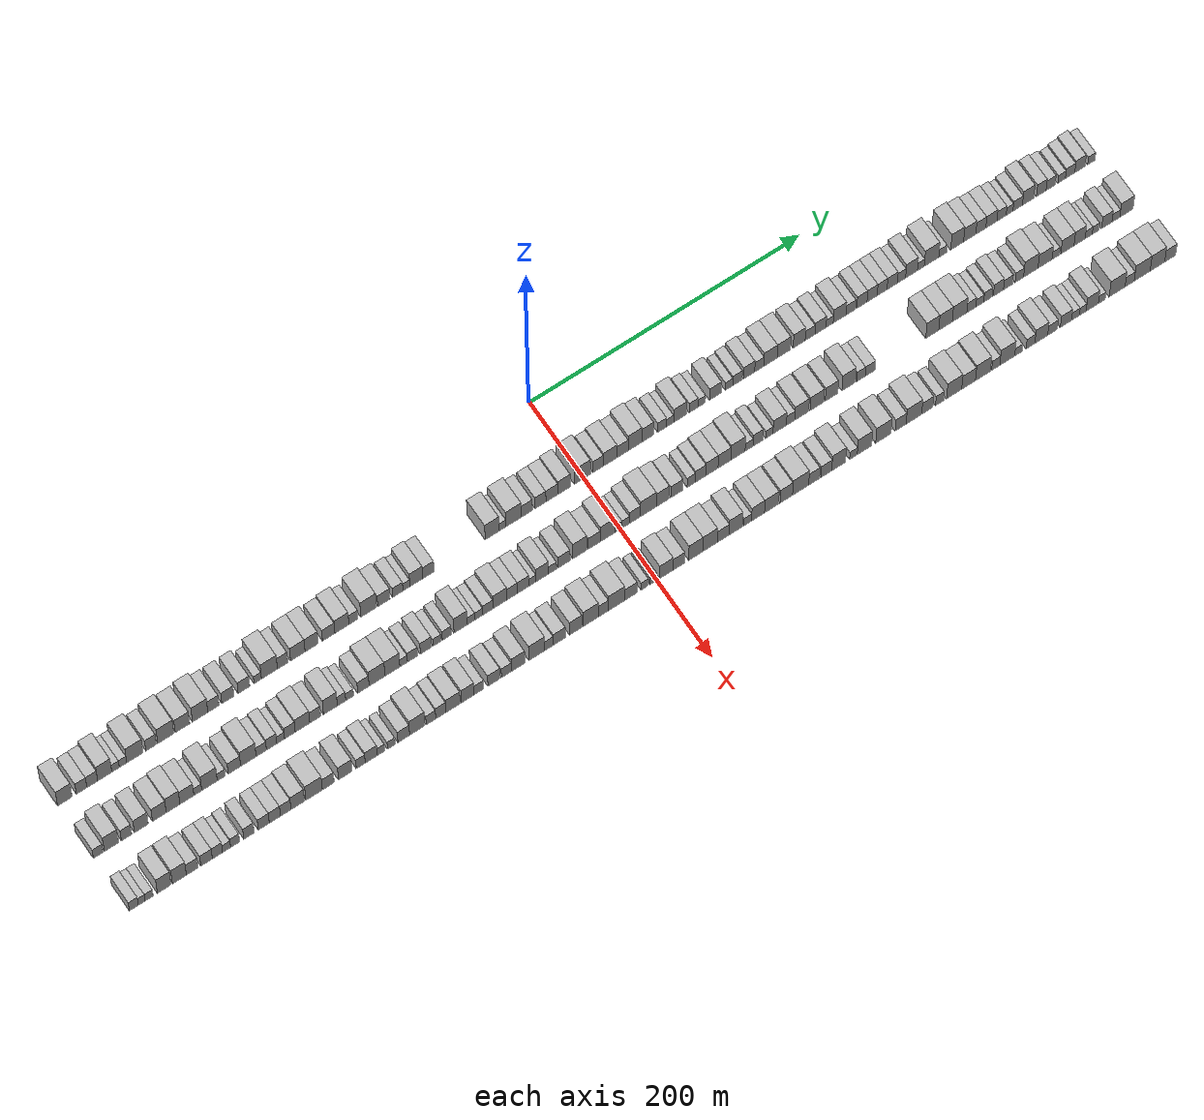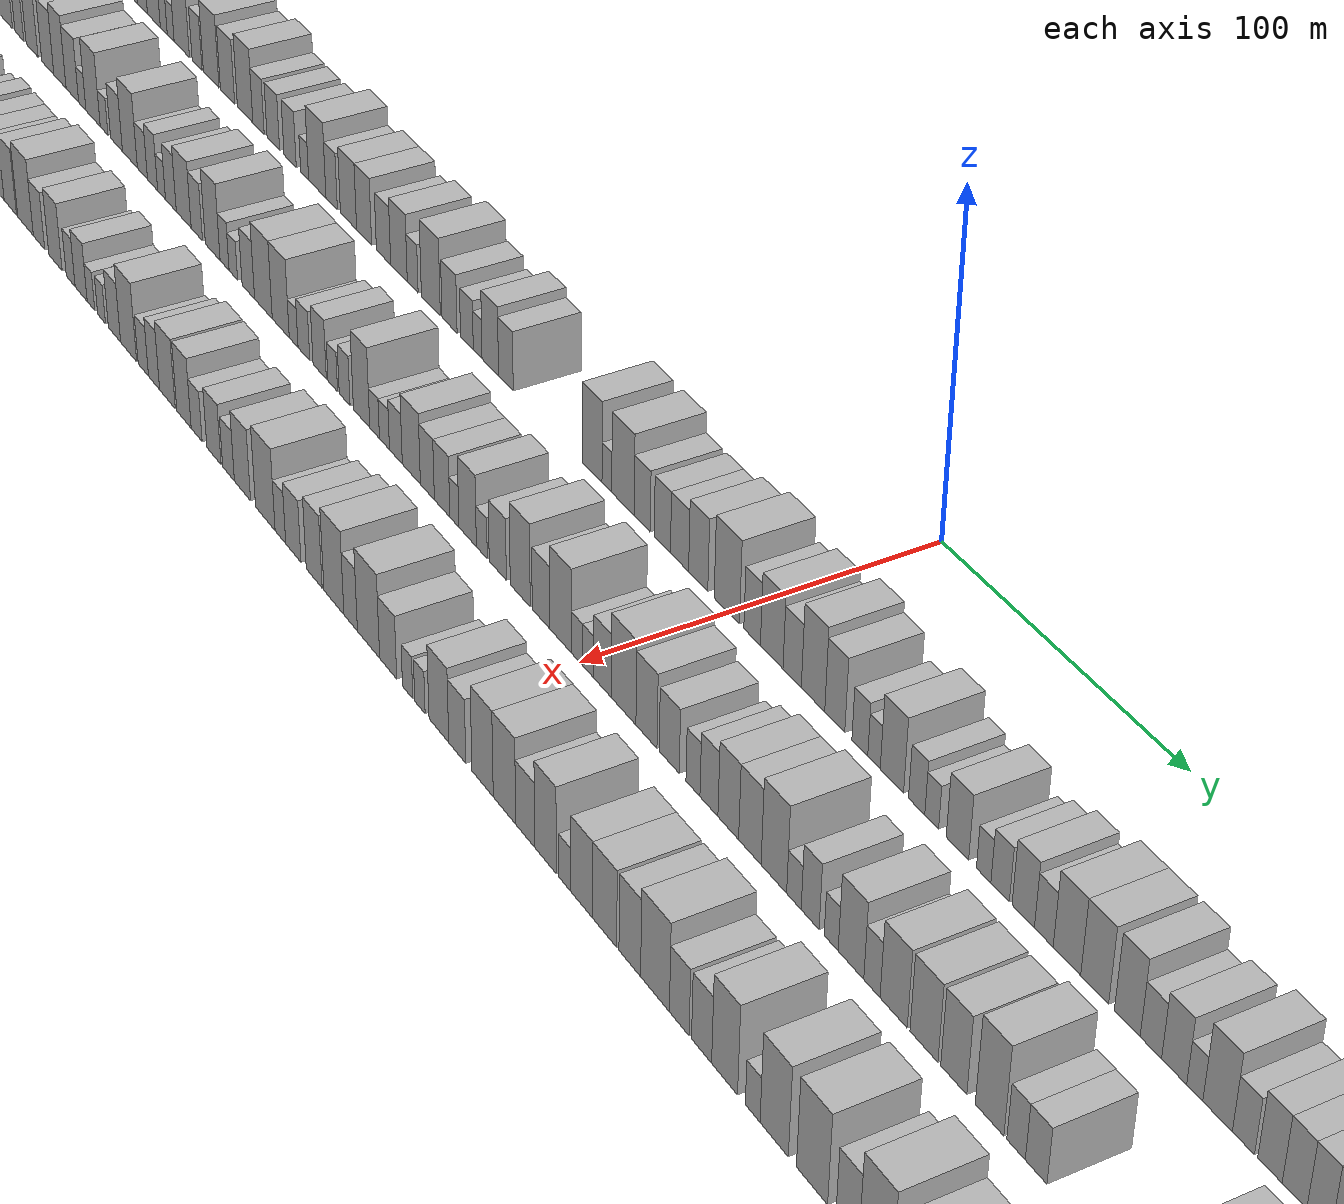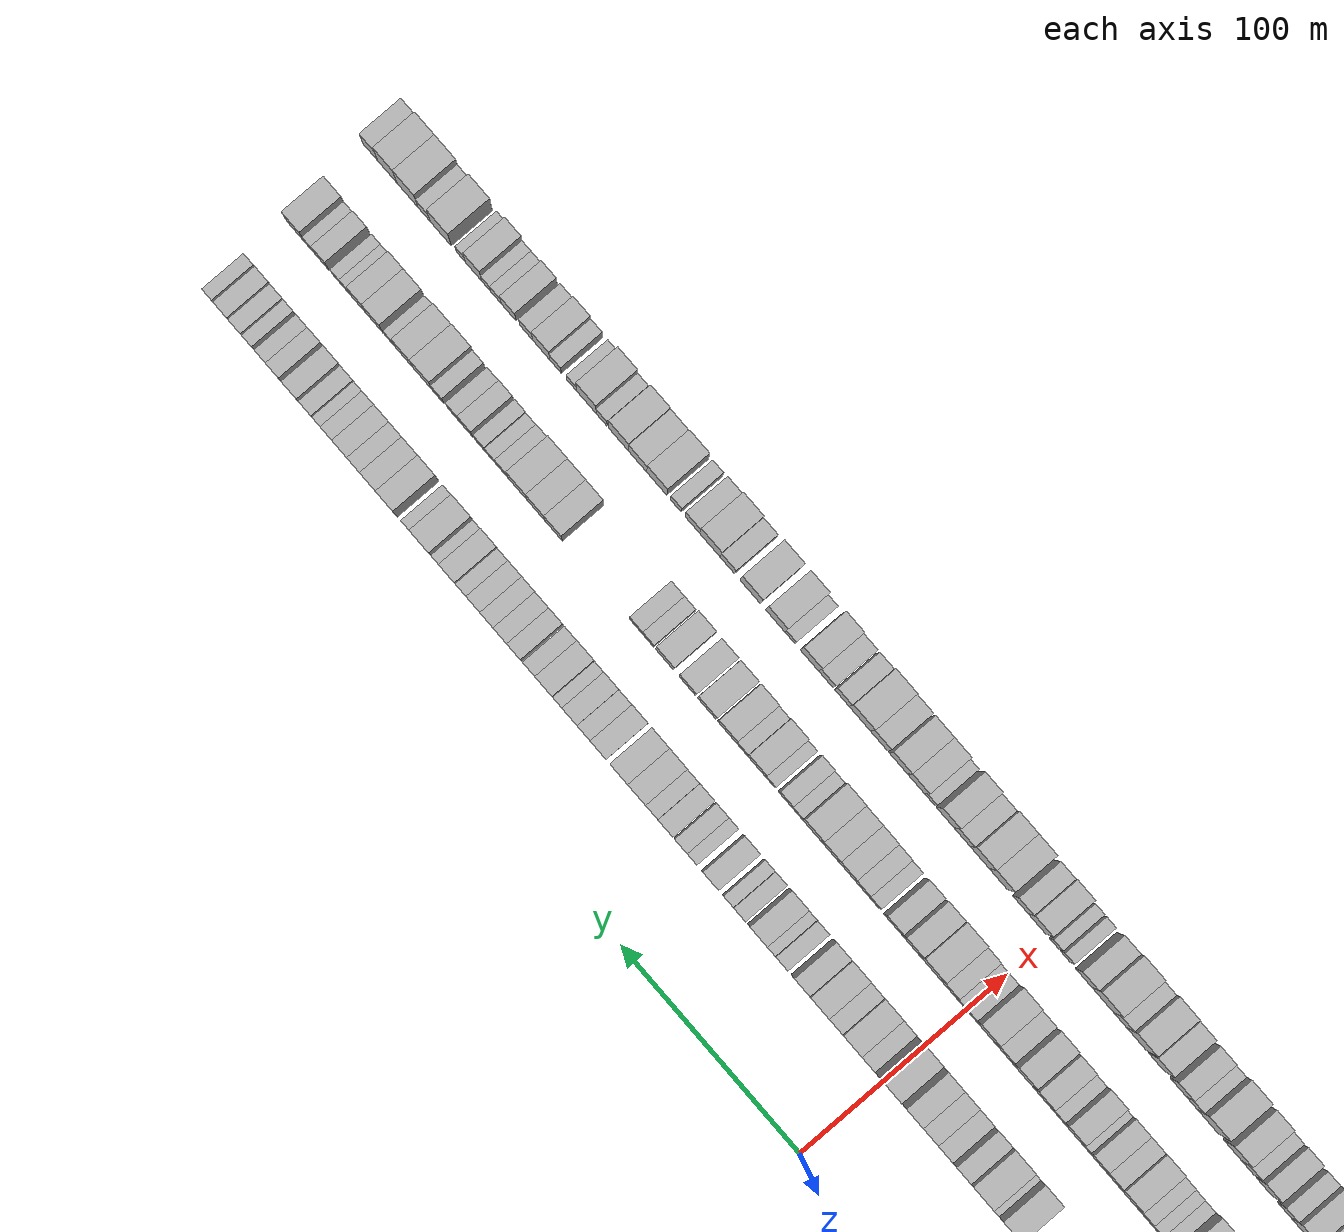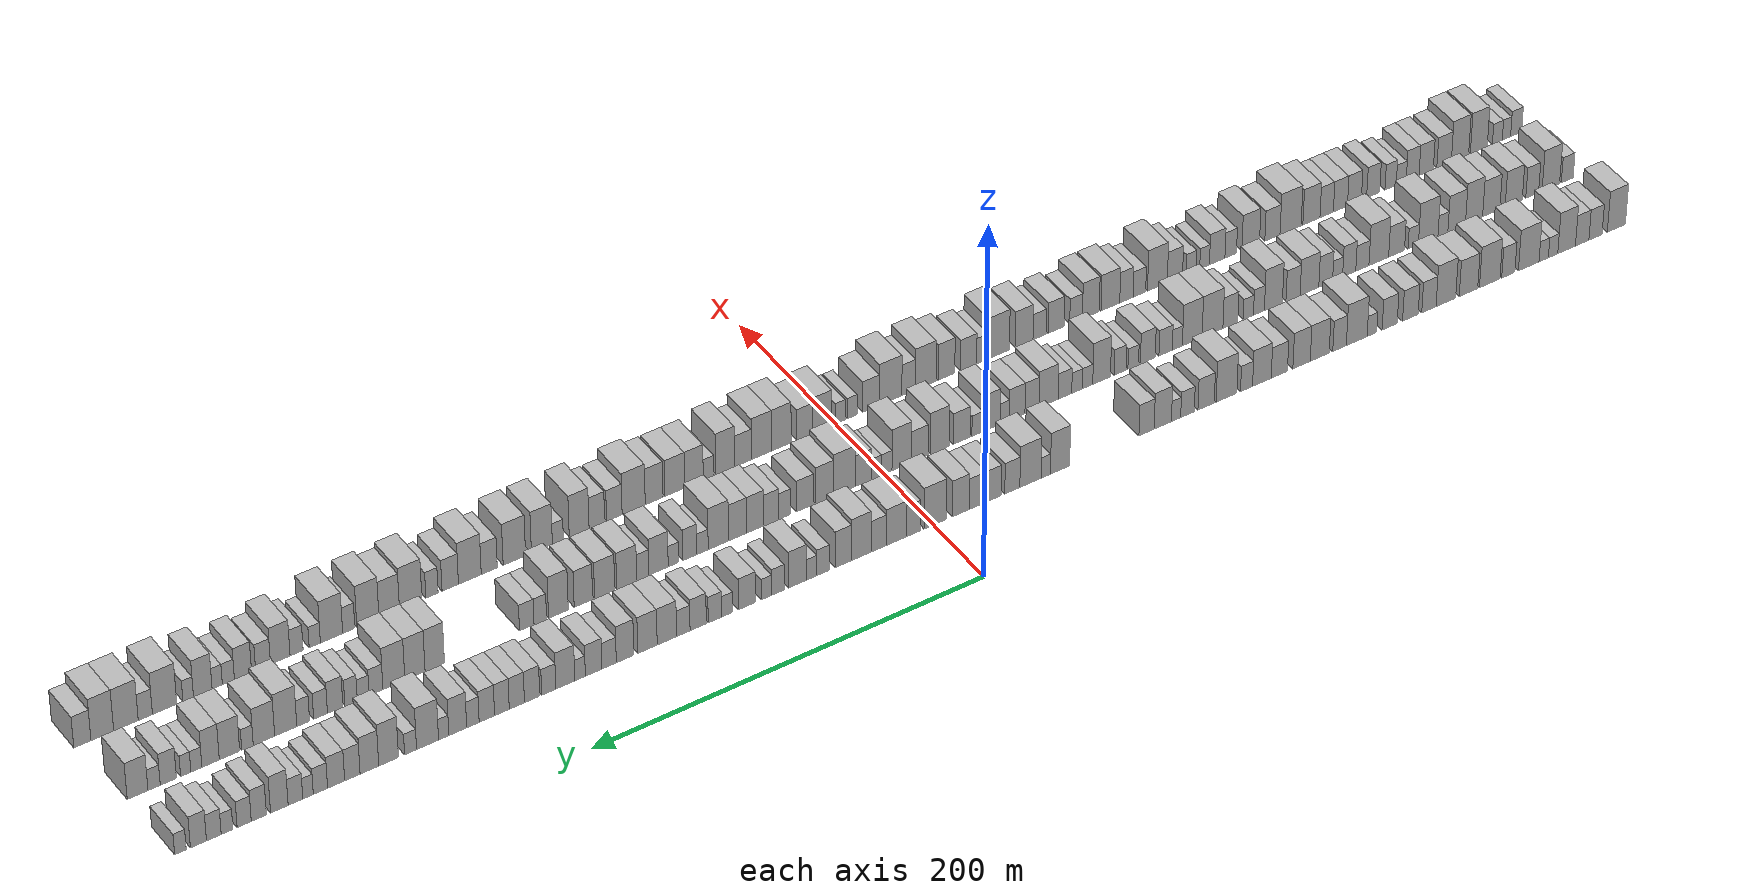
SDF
<sdf version="1.6">
 <world name="default">
  <scene>
   <sky><clouds><speed>12</speed></clouds></sky>
   <ambient>0.4 0.4 0.4 1</ambient>
   <background>0.7 0.7 0.7 1</background>
   <shadows>1</shadows>
  </scene>
  <gravity>0 0 -9.8066</gravity>
  <magnetic_field>6e-06 2.3e-05 -4.2e-05</magnetic_field>
  <physics default="0" name="default_physics" type="ode">
   <ode>
    <solver>
     <type>quick</type>
     <iters>10</iters>
     <sor>1.0</sor>
     <use_dynamic_moi_rescaling>0</use_dynamic_moi_rescaling>
    </solver>
    <constraints>
     <cfm>0</cfm>
     <erp>0.2</erp>
     <contact_max_correcting_vel>100</contact_max_correcting_vel>
     <contact_surface_layer>0.001</contact_surface_layer>
    </constraints>
   </ode>
   <max_step_size>0.004</max_step_size>
   <real_time_factor>1</real_time_factor>
   <real_time_update_rate>250</real_time_update_rate>
  </physics>
  <light name="sun" type="directional">
   <pose>0 0 10 0 0 0</pose>
   <diffuse>0.8 0.8 0.8 1</diffuse>
   <specular>0.2 0.2 0.2 1</specular>
   <attenuation>
    <range>1000</range>
    <constant>0.9</constant>
    <linear>0.01</linear>
    <quadratic>0.001</quadratic>
   </attenuation>
   <direction>-0.5 0.1 -0.9</direction>
  </light>
  <model name="building_1">
   <static>1</static>
   <pose>50.0000 -374.8134 0 0.000000 0.000000 0.000000</pose>
   <link name="link">
    <pose>0 0 12.00 0 0 0</pose>
    <collision name="collision"><geometry><box><size>20.0000 10.3733 24.0000</size></box></geometry></collision>
    <visual name="visual">
     <cast_shadows>0</cast_shadows>
     <geometry><box><size>20.0000 10.3733 24.0000</size></box></geometry>
     <material>
      <script>
       <uri>model://HANNAS_wall/materials/scripts</uri>
       <uri>model://HANNAS_wall/materials/textures</uri>
       <name>vrc/HANNAS_wall</name>
      </script>
     </material>
    </visual>
   </link>
  </model>
  <model name="building_2">
   <static>1</static>
   <pose>50.0000 -362.8663 0 0.000000 0.000000 0.000000</pose>
   <link name="link">
    <pose>0 0 9.00 0 0 0</pose>
    <collision name="collision"><geometry><box><size>20.0000 7.5209 18.0000</size></box></geometry></collision>
    <visual name="visual">
     <cast_shadows>0</cast_shadows>
     <geometry><box><size>20.0000 7.5209 18.0000</size></box></geometry>
     <material>
      <script>
       <uri>model://HANNAS_wall/materials/scripts</uri>
       <uri>model://HANNAS_wall/materials/textures</uri>
       <name>vrc/HANNAS_wall</name>
      </script>
     </material>
    </visual>
   </link>
  </model>
  <model name="building_3">
   <static>1</static>
   <pose>50.0000 -355.2702 0 0.000000 0.000000 0.000000</pose>
   <link name="link">
    <pose>0 0 9.00 0 0 0</pose>
    <collision name="collision"><geometry><box><size>20.0000 7.6712 18.0000</size></box></geometry></collision>
    <visual name="visual">
     <cast_shadows>0</cast_shadows>
     <geometry><box><size>20.0000 7.6712 18.0000</size></box></geometry>
     <material>
      <script>
       <uri>model://HANNAS_wall/materials/scripts</uri>
       <uri>model://HANNAS_wall/materials/textures</uri>
       <name>vrc/HANNAS_wall</name>
      </script>
     </material>
    </visual>
   </link>
  </model>
  <model name="building_4">
   <static>1</static>
   <pose>50.0000 -346.3979 0 0.000000 0.000000 0.000000</pose>
   <link name="link">
    <pose>0 0 12.00 0 0 0</pose>
    <collision name="collision"><geometry><box><size>20.0000 10.0734 24.0000</size></box></geometry></collision>
    <visual name="visual">
     <cast_shadows>0</cast_shadows>
     <geometry><box><size>20.0000 10.0734 24.0000</size></box></geometry>
     <material>
      <script>
       <uri>model://HANNAS_wall/materials/scripts</uri>
       <uri>model://HANNAS_wall/materials/textures</uri>
       <name>vrc/HANNAS_wall</name>
      </script>
     </material>
    </visual>
   </link>
  </model>
  <model name="building_5">
   <static>1</static>
   <pose>50.0000 -338.6810 0 0.000000 0.000000 0.000000</pose>
   <link name="link">
    <pose>0 0 6.00 0 0 0</pose>
    <collision name="collision"><geometry><box><size>20.0000 5.3604 12.0000</size></box></geometry></collision>
    <visual name="visual">
     <cast_shadows>0</cast_shadows>
     <geometry><box><size>20.0000 5.3604 12.0000</size></box></geometry>
     <material>
      <script>
       <uri>model://HANNAS_wall/materials/scripts</uri>
       <uri>model://HANNAS_wall/materials/textures</uri>
       <name>vrc/HANNAS_wall</name>
      </script>
     </material>
    </visual>
   </link>
  </model>
  <model name="building_6">
   <static>1</static>
   <pose>50.0000 -333.3382 0 0.000000 0.000000 0.000000</pose>
   <link name="link">
    <pose>0 0 6.00 0 0 0</pose>
    <collision name="collision"><geometry><box><size>20.0000 5.3252 12.0000</size></box></geometry></collision>
    <visual name="visual">
     <cast_shadows>0</cast_shadows>
     <geometry><box><size>20.0000 5.3252 12.0000</size></box></geometry>
     <material>
      <script>
       <uri>model://HANNAS_wall/materials/scripts</uri>
       <uri>model://HANNAS_wall/materials/textures</uri>
       <name>vrc/HANNAS_wall</name>
      </script>
     </material>
    </visual>
   </link>
  </model>
  <model name="building_7">
   <static>1</static>
   <pose>50.0000 -324.8384 0 0.000000 0.000000 0.000000</pose>
   <link name="link">
    <pose>0 0 12.00 0 0 0</pose>
    <collision name="collision"><geometry><box><size>20.0000 11.6744 24.0000</size></box></geometry></collision>
    <visual name="visual">
     <cast_shadows>0</cast_shadows>
     <geometry><box><size>20.0000 11.6744 24.0000</size></box></geometry>
     <material>
      <script>
       <uri>model://HANNAS_wall/materials/scripts</uri>
       <uri>model://HANNAS_wall/materials/textures</uri>
       <name>vrc/HANNAS_wall</name>
      </script>
     </material>
    </visual>
   </link>
  </model>
  <model name="building_8">
   <static>1</static>
   <pose>50.0000 -313.2694 0 0.000000 0.000000 0.000000</pose>
   <link name="link">
    <pose>0 0 9.00 0 0 0</pose>
    <collision name="collision"><geometry><box><size>20.0000 7.4635 18.0000</size></box></geometry></collision>
    <visual name="visual">
     <cast_shadows>0</cast_shadows>
     <geometry><box><size>20.0000 7.4635 18.0000</size></box></geometry>
     <material>
      <script>
       <uri>model://HANNAS_wall/materials/scripts</uri>
       <uri>model://HANNAS_wall/materials/textures</uri>
       <name>vrc/HANNAS_wall</name>
      </script>
     </material>
    </visual>
   </link>
  </model>
  <model name="building_9">
   <static>1</static>
   <pose>50.0000 -302.7648 0 0.000000 0.000000 0.000000</pose>
   <link name="link">
    <pose>0 0 12.00 0 0 0</pose>
    <collision name="collision"><geometry><box><size>20.0000 11.5457 24.0000</size></box></geometry></collision>
    <visual name="visual">
     <cast_shadows>0</cast_shadows>
     <geometry><box><size>20.0000 11.5457 24.0000</size></box></geometry>
     <material>
      <script>
       <uri>model://HANNAS_wall/materials/scripts</uri>
       <uri>model://HANNAS_wall/materials/textures</uri>
       <name>vrc/HANNAS_wall</name>
      </script>
     </material>
    </visual>
   </link>
  </model>
  <model name="building_10">
   <static>1</static>
   <pose>50.0000 -290.8009 0 0.000000 0.000000 0.000000</pose>
   <link name="link">
    <pose>0 0 10.50 0 0 0</pose>
    <collision name="collision"><geometry><box><size>20.0000 10.3822 21.0000</size></box></geometry></collision>
    <visual name="visual">
     <cast_shadows>0</cast_shadows>
     <geometry><box><size>20.0000 10.3822 21.0000</size></box></geometry>
     <material>
      <script>
       <uri>model://HANNAS_wall/materials/scripts</uri>
       <uri>model://HANNAS_wall/materials/textures</uri>
       <name>vrc/HANNAS_wall</name>
      </script>
     </material>
    </visual>
   </link>
  </model>
  <model name="building_11">
   <static>1</static>
   <pose>50.0000 -278.0995 0 0.000000 0.000000 0.000000</pose>
   <link name="link">
    <pose>0 0 12.00 0 0 0</pose>
    <collision name="collision"><geometry><box><size>20.0000 11.0205 24.0000</size></box></geometry></collision>
    <visual name="visual">
     <cast_shadows>0</cast_shadows>
     <geometry><box><size>20.0000 11.0205 24.0000</size></box></geometry>
     <material>
      <script>
       <uri>model://HANNAS_wall/materials/scripts</uri>
       <uri>model://HANNAS_wall/materials/textures</uri>
       <name>vrc/HANNAS_wall</name>
      </script>
     </material>
    </visual>
   </link>
  </model>
  <model name="building_12">
   <static>1</static>
   <pose>50.0000 -268.5931 0 0.000000 0.000000 0.000000</pose>
   <link name="link">
    <pose>0 0 9.00 0 0 0</pose>
    <collision name="collision"><geometry><box><size>20.0000 7.9923 18.0000</size></box></geometry></collision>
    <visual name="visual">
     <cast_shadows>0</cast_shadows>
     <geometry><box><size>20.0000 7.9923 18.0000</size></box></geometry>
     <material>
      <script>
       <uri>model://HANNAS_wall/materials/scripts</uri>
       <uri>model://HANNAS_wall/materials/textures</uri>
       <name>vrc/HANNAS_wall</name>
      </script>
     </material>
    </visual>
   </link>
  </model>
  <model name="building_13">
   <static>1</static>
   <pose>50.0000 -258.2329 0 0.000000 0.000000 0.000000</pose>
   <link name="link">
    <pose>0 0 9.00 0 0 0</pose>
    <collision name="collision"><geometry><box><size>20.0000 8.7283 18.0000</size></box></geometry></collision>
    <visual name="visual">
     <cast_shadows>0</cast_shadows>
     <geometry><box><size>20.0000 8.7283 18.0000</size></box></geometry>
     <material>
      <script>
       <uri>model://HANNAS_wall/materials/scripts</uri>
       <uri>model://HANNAS_wall/materials/textures</uri>
       <name>vrc/HANNAS_wall</name>
      </script>
     </material>
    </visual>
   </link>
  </model>
  <model name="building_14">
   <static>1</static>
   <pose>50.0000 -246.6707 0 0.000000 0.000000 0.000000</pose>
   <link name="link">
    <pose>0 0 9.00 0 0 0</pose>
    <collision name="collision"><geometry><box><size>20.0000 8.3961 18.0000</size></box></geometry></collision>
    <visual name="visual">
     <cast_shadows>0</cast_shadows>
     <geometry><box><size>20.0000 8.3961 18.0000</size></box></geometry>
     <material>
      <script>
       <uri>model://HANNAS_wall/materials/scripts</uri>
       <uri>model://HANNAS_wall/materials/textures</uri>
       <name>vrc/HANNAS_wall</name>
      </script>
     </material>
    </visual>
   </link>
  </model>
  <model name="building_15">
   <static>1</static>
   <pose>50.0000 -236.7995 0 0.000000 0.000000 0.000000</pose>
   <link name="link">
    <pose>0 0 6.00 0 0 0</pose>
    <collision name="collision"><geometry><box><size>20.0000 5.3462 12.0000</size></box></geometry></collision>
    <visual name="visual">
     <cast_shadows>0</cast_shadows>
     <geometry><box><size>20.0000 5.3462 12.0000</size></box></geometry>
     <material>
      <script>
       <uri>model://HANNAS_wall/materials/scripts</uri>
       <uri>model://HANNAS_wall/materials/textures</uri>
       <name>vrc/HANNAS_wall</name>
      </script>
     </material>
    </visual>
   </link>
  </model>
  <model name="building_16">
   <static>1</static>
   <pose>50.0000 -228.3568 0 0.000000 0.000000 0.000000</pose>
   <link name="link">
    <pose>0 0 12.00 0 0 0</pose>
    <collision name="collision"><geometry><box><size>20.0000 11.5392 24.0000</size></box></geometry></collision>
    <visual name="visual">
     <cast_shadows>0</cast_shadows>
     <geometry><box><size>20.0000 11.5392 24.0000</size></box></geometry>
     <material>
      <script>
       <uri>model://HANNAS_wall/materials/scripts</uri>
       <uri>model://HANNAS_wall/materials/textures</uri>
       <name>vrc/HANNAS_wall</name>
      </script>
     </material>
    </visual>
   </link>
  </model>
  <model name="building_17">
   <static>1</static>
   <pose>50.0000 -218.8502 0 0.000000 0.000000 0.000000</pose>
   <link name="link">
    <pose>0 0 9.00 0 0 0</pose>
    <collision name="collision"><geometry><box><size>20.0000 7.4741 18.0000</size></box></geometry></collision>
    <visual name="visual">
     <cast_shadows>0</cast_shadows>
     <geometry><box><size>20.0000 7.4741 18.0000</size></box></geometry>
     <material>
      <script>
       <uri>model://HANNAS_wall/materials/scripts</uri>
       <uri>model://HANNAS_wall/materials/textures</uri>
       <name>vrc/HANNAS_wall</name>
      </script>
     </material>
    </visual>
   </link>
  </model>
  <model name="building_18">
   <static>1</static>
   <pose>50.0000 -207.8882 0 0.000000 0.000000 0.000000</pose>
   <link name="link">
    <pose>0 0 10.50 0 0 0</pose>
    <collision name="collision"><geometry><box><size>20.0000 10.4499 21.0000</size></box></geometry></collision>
    <visual name="visual">
     <cast_shadows>0</cast_shadows>
     <geometry><box><size>20.0000 10.4499 21.0000</size></box></geometry>
     <material>
      <script>
       <uri>model://HANNAS_wall/materials/scripts</uri>
       <uri>model://HANNAS_wall/materials/textures</uri>
       <name>vrc/HANNAS_wall</name>
      </script>
     </material>
    </visual>
   </link>
  </model>
  <model name="building_19">
   <static>1</static>
   <pose>50.0000 -197.8814 0 0.000000 0.000000 0.000000</pose>
   <link name="link">
    <pose>0 0 10.50 0 0 0</pose>
    <collision name="collision"><geometry><box><size>20.0000 9.5638 21.0000</size></box></geometry></collision>
    <visual name="visual">
     <cast_shadows>0</cast_shadows>
     <geometry><box><size>20.0000 9.5638 21.0000</size></box></geometry>
     <material>
      <script>
       <uri>model://HANNAS_wall/materials/scripts</uri>
       <uri>model://HANNAS_wall/materials/textures</uri>
       <name>vrc/HANNAS_wall</name>
      </script>
     </material>
    </visual>
   </link>
  </model>
  <model name="building_20">
   <static>1</static>
   <pose>50.0000 -185.6342 0 0.000000 0.000000 0.000000</pose>
   <link name="link">
    <pose>0 0 9.00 0 0 0</pose>
    <collision name="collision"><geometry><box><size>20.0000 8.9306 18.0000</size></box></geometry></collision>
    <visual name="visual">
     <cast_shadows>0</cast_shadows>
     <geometry><box><size>20.0000 8.9306 18.0000</size></box></geometry>
     <material>
      <script>
       <uri>model://HANNAS_wall/materials/scripts</uri>
       <uri>model://HANNAS_wall/materials/textures</uri>
       <name>vrc/HANNAS_wall</name>
      </script>
     </material>
    </visual>
   </link>
  </model>
  <model name="building_21">
   <static>1</static>
   <pose>50.0000 -176.0748 0 0.000000 0.000000 0.000000</pose>
   <link name="link">
    <pose>0 0 10.50 0 0 0</pose>
    <collision name="collision"><geometry><box><size>20.0000 10.1881 21.0000</size></box></geometry></collision>
    <visual name="visual">
     <cast_shadows>0</cast_shadows>
     <geometry><box><size>20.0000 10.1881 21.0000</size></box></geometry>
     <material>
      <script>
       <uri>model://HANNAS_wall/materials/scripts</uri>
       <uri>model://HANNAS_wall/materials/textures</uri>
       <name>vrc/HANNAS_wall</name>
      </script>
     </material>
    </visual>
   </link>
  </model>
  <model name="building_22">
   <static>1</static>
   <pose>50.0000 -167.6846 0 0.000000 0.000000 0.000000</pose>
   <link name="link">
    <pose>0 0 7.50 0 0 0</pose>
    <collision name="collision"><geometry><box><size>20.0000 6.5922 15.0000</size></box></geometry></collision>
    <visual name="visual">
     <cast_shadows>0</cast_shadows>
     <geometry><box><size>20.0000 6.5922 15.0000</size></box></geometry>
     <material>
      <script>
       <uri>model://HANNAS_wall/materials/scripts</uri>
       <uri>model://HANNAS_wall/materials/textures</uri>
       <name>vrc/HANNAS_wall</name>
      </script>
     </material>
    </visual>
   </link>
  </model>
  <model name="building_23">
   <static>1</static>
   <pose>50.0000 -156.7351 0 0.000000 0.000000 0.000000</pose>
   <link name="link">
    <pose>0 0 12.00 0 0 0</pose>
    <collision name="collision"><geometry><box><size>20.0000 11.3069 24.0000</size></box></geometry></collision>
    <visual name="visual">
     <cast_shadows>0</cast_shadows>
     <geometry><box><size>20.0000 11.3069 24.0000</size></box></geometry>
     <material>
      <script>
       <uri>model://HANNAS_wall/materials/scripts</uri>
       <uri>model://HANNAS_wall/materials/textures</uri>
       <name>vrc/HANNAS_wall</name>
      </script>
     </material>
    </visual>
   </link>
  </model>
  <model name="building_24">
   <static>1</static>
   <pose>50.0000 -145.6544 0 0.000000 0.000000 0.000000</pose>
   <link name="link">
    <pose>0 0 9.00 0 0 0</pose>
    <collision name="collision"><geometry><box><size>20.0000 8.8546 18.0000</size></box></geometry></collision>
    <visual name="visual">
     <cast_shadows>0</cast_shadows>
     <geometry><box><size>20.0000 8.8546 18.0000</size></box></geometry>
     <material>
      <script>
       <uri>model://HANNAS_wall/materials/scripts</uri>
       <uri>model://HANNAS_wall/materials/textures</uri>
       <name>vrc/HANNAS_wall</name>
      </script>
     </material>
    </visual>
   </link>
  </model>
  <model name="building_25">
   <static>1</static>
   <pose>50.0000 -135.5362 0 0.000000 0.000000 0.000000</pose>
   <link name="link">
    <pose>0 0 7.50 0 0 0</pose>
    <collision name="collision"><geometry><box><size>20.0000 7.3818 15.0000</size></box></geometry></collision>
    <visual name="visual">
     <cast_shadows>0</cast_shadows>
     <geometry><box><size>20.0000 7.3818 15.0000</size></box></geometry>
     <material>
      <script>
       <uri>model://HANNAS_wall/materials/scripts</uri>
       <uri>model://HANNAS_wall/materials/textures</uri>
       <name>vrc/HANNAS_wall</name>
      </script>
     </material>
    </visual>
   </link>
  </model>
  <model name="building_26">
   <static>1</static>
   <pose>50.0000 -129.3392 0 0.000000 0.000000 0.000000</pose>
   <link name="link">
    <pose>0 0 6.00 0 0 0</pose>
    <collision name="collision"><geometry><box><size>20.0000 5.0122 12.0000</size></box></geometry></collision>
    <visual name="visual">
     <cast_shadows>0</cast_shadows>
     <geometry><box><size>20.0000 5.0122 12.0000</size></box></geometry>
     <material>
      <script>
       <uri>model://HANNAS_wall/materials/scripts</uri>
       <uri>model://HANNAS_wall/materials/textures</uri>
       <name>vrc/HANNAS_wall</name>
      </script>
     </material>
    </visual>
   </link>
  </model>
  <model name="building_27">
   <static>1</static>
   <pose>50.0000 -122.1619 0 0.000000 0.000000 0.000000</pose>
   <link name="link">
    <pose>0 0 10.50 0 0 0</pose>
    <collision name="collision"><geometry><box><size>20.0000 9.3425 21.0000</size></box></geometry></collision>
    <visual name="visual">
     <cast_shadows>0</cast_shadows>
     <geometry><box><size>20.0000 9.3425 21.0000</size></box></geometry>
     <material>
      <script>
       <uri>model://HANNAS_wall/materials/scripts</uri>
       <uri>model://HANNAS_wall/materials/textures</uri>
       <name>vrc/HANNAS_wall</name>
      </script>
     </material>
    </visual>
   </link>
  </model>
  <model name="building_28">
   <static>1</static>
   <pose>50.0000 -113.3848 0 0.000000 0.000000 0.000000</pose>
   <link name="link">
    <pose>0 0 9.00 0 0 0</pose>
    <collision name="collision"><geometry><box><size>20.0000 8.2117 18.0000</size></box></geometry></collision>
    <visual name="visual">
     <cast_shadows>0</cast_shadows>
     <geometry><box><size>20.0000 8.2117 18.0000</size></box></geometry>
     <material>
      <script>
       <uri>model://HANNAS_wall/materials/scripts</uri>
       <uri>model://HANNAS_wall/materials/textures</uri>
       <name>vrc/HANNAS_wall</name>
      </script>
     </material>
    </visual>
   </link>
  </model>
  <model name="building_29">
   <static>1</static>
   <pose>50.0000 -66.9518 0 0.000000 0.000000 0.000000</pose>
   <link name="link">
    <pose>0 0 12.00 0 0 0</pose>
    <collision name="collision"><geometry><box><size>20.0000 10.2181 24.0000</size></box></geometry></collision>
    <visual name="visual">
     <cast_shadows>0</cast_shadows>
     <geometry><box><size>20.0000 10.2181 24.0000</size></box></geometry>
     <material>
      <script>
       <uri>model://HANNAS_wall/materials/scripts</uri>
       <uri>model://HANNAS_wall/materials/textures</uri>
       <name>vrc/HANNAS_wall</name>
      </script>
     </material>
    </visual>
   </link>
  </model>
  <model name="building_30">
   <static>1</static>
   <pose>50.0000 -59.3542 0 0.000000 0.000000 0.000000</pose>
   <link name="link">
    <pose>0 0 6.00 0 0 0</pose>
    <collision name="collision"><geometry><box><size>20.0000 4.9770 12.0000</size></box></geometry></collision>
    <visual name="visual">
     <cast_shadows>0</cast_shadows>
     <geometry><box><size>20.0000 4.9770 12.0000</size></box></geometry>
     <material>
      <script>
       <uri>model://HANNAS_wall/materials/scripts</uri>
       <uri>model://HANNAS_wall/materials/textures</uri>
       <name>vrc/HANNAS_wall</name>
      </script>
     </material>
    </visual>
   </link>
  </model>
  <model name="building_31">
   <static>1</static>
   <pose>50.0000 -51.2099 0 0.000000 0.000000 0.000000</pose>
   <link name="link">
    <pose>0 0 12.00 0 0 0</pose>
    <collision name="collision"><geometry><box><size>20.0000 11.3114 24.0000</size></box></geometry></collision>
    <visual name="visual">
     <cast_shadows>0</cast_shadows>
     <geometry><box><size>20.0000 11.3114 24.0000</size></box></geometry>
     <material>
      <script>
       <uri>model://HANNAS_wall/materials/scripts</uri>
       <uri>model://HANNAS_wall/materials/textures</uri>
       <name>vrc/HANNAS_wall</name>
      </script>
     </material>
    </visual>
   </link>
  </model>
  <model name="building_32">
   <static>1</static>
   <pose>50.0000 -41.5600 0 0.000000 0.000000 0.000000</pose>
   <link name="link">
    <pose>0 0 9.00 0 0 0</pose>
    <collision name="collision"><geometry><box><size>20.0000 7.9885 18.0000</size></box></geometry></collision>
    <visual name="visual">
     <cast_shadows>0</cast_shadows>
     <geometry><box><size>20.0000 7.9885 18.0000</size></box></geometry>
     <material>
      <script>
       <uri>model://HANNAS_wall/materials/scripts</uri>
       <uri>model://HANNAS_wall/materials/textures</uri>
       <name>vrc/HANNAS_wall</name>
      </script>
     </material>
    </visual>
   </link>
  </model>
  <model name="building_33">
   <static>1</static>
   <pose>50.0000 -31.6120 0 0.000000 0.000000 0.000000</pose>
   <link name="link">
    <pose>0 0 9.00 0 0 0</pose>
    <collision name="collision"><geometry><box><size>20.0000 7.9074 18.0000</size></box></geometry></collision>
    <visual name="visual">
     <cast_shadows>0</cast_shadows>
     <geometry><box><size>20.0000 7.9074 18.0000</size></box></geometry>
     <material>
      <script>
       <uri>model://HANNAS_wall/materials/scripts</uri>
       <uri>model://HANNAS_wall/materials/textures</uri>
       <name>vrc/HANNAS_wall</name>
      </script>
     </material>
    </visual>
   </link>
  </model>
  <model name="building_34">
   <static>1</static>
   <pose>50.0000 -23.2832 0 0.000000 0.000000 0.000000</pose>
   <link name="link">
    <pose>0 0 9.00 0 0 0</pose>
    <collision name="collision"><geometry><box><size>20.0000 8.7502 18.0000</size></box></geometry></collision>
    <visual name="visual">
     <cast_shadows>0</cast_shadows>
     <geometry><box><size>20.0000 8.7502 18.0000</size></box></geometry>
     <material>
      <script>
       <uri>model://HANNAS_wall/materials/scripts</uri>
       <uri>model://HANNAS_wall/materials/textures</uri>
       <name>vrc/HANNAS_wall</name>
      </script>
     </material>
    </visual>
   </link>
  </model>
  <model name="building_35">
   <static>1</static>
   <pose>50.0000 -14.3598 0 0.000000 0.000000 0.000000</pose>
   <link name="link">
    <pose>0 0 10.50 0 0 0</pose>
    <collision name="collision"><geometry><box><size>20.0000 9.0968 21.0000</size></box></geometry></collision>
    <visual name="visual">
     <cast_shadows>0</cast_shadows>
     <geometry><box><size>20.0000 9.0968 21.0000</size></box></geometry>
     <material>
      <script>
       <uri>model://HANNAS_wall/materials/scripts</uri>
       <uri>model://HANNAS_wall/materials/textures</uri>
       <name>vrc/HANNAS_wall</name>
      </script>
     </material>
    </visual>
   </link>
  </model>
  <model name="building_36">
   <static>1</static>
   <pose>50.0000 -0.9406 0 0.000000 0.000000 0.000000</pose>
   <link name="link">
    <pose>0 0 12.00 0 0 0</pose>
    <collision name="collision"><geometry><box><size>20.0000 11.7416 24.0000</size></box></geometry></collision>
    <visual name="visual">
     <cast_shadows>0</cast_shadows>
     <geometry><box><size>20.0000 11.7416 24.0000</size></box></geometry>
     <material>
      <script>
       <uri>model://HANNAS_wall/materials/scripts</uri>
       <uri>model://HANNAS_wall/materials/textures</uri>
       <name>vrc/HANNAS_wall</name>
      </script>
     </material>
    </visual>
   </link>
  </model>
  <model name="building_37">
   <static>1</static>
   <pose>50.0000 10.6920 0 0.000000 0.000000 0.000000</pose>
   <link name="link">
    <pose>0 0 9.00 0 0 0</pose>
    <collision name="collision"><geometry><box><size>20.0000 7.5236 18.0000</size></box></geometry></collision>
    <visual name="visual">
     <cast_shadows>0</cast_shadows>
     <geometry><box><size>20.0000 7.5236 18.0000</size></box></geometry>
     <material>
      <script>
       <uri>model://HANNAS_wall/materials/scripts</uri>
       <uri>model://HANNAS_wall/materials/textures</uri>
       <name>vrc/HANNAS_wall</name>
      </script>
     </material>
    </visual>
   </link>
  </model>
  <model name="building_38">
   <static>1</static>
   <pose>50.0000 19.5133 0 0.000000 0.000000 0.000000</pose>
   <link name="link">
    <pose>0 0 10.50 0 0 0</pose>
    <collision name="collision"><geometry><box><size>20.0000 10.1190 21.0000</size></box></geometry></collision>
    <visual name="visual">
     <cast_shadows>0</cast_shadows>
     <geometry><box><size>20.0000 10.1190 21.0000</size></box></geometry>
     <material>
      <script>
       <uri>model://HANNAS_wall/materials/scripts</uri>
       <uri>model://HANNAS_wall/materials/textures</uri>
       <name>vrc/HANNAS_wall</name>
      </script>
     </material>
    </visual>
   </link>
  </model>
  <model name="building_39">
   <static>1</static>
   <pose>50.0000 28.5930 0 0.000000 0.000000 0.000000</pose>
   <link name="link">
    <pose>0 0 9.00 0 0 0</pose>
    <collision name="collision"><geometry><box><size>20.0000 8.0403 18.0000</size></box></geometry></collision>
    <visual name="visual">
     <cast_shadows>0</cast_shadows>
     <geometry><box><size>20.0000 8.0403 18.0000</size></box></geometry>
     <material>
      <script>
       <uri>model://HANNAS_wall/materials/scripts</uri>
       <uri>model://HANNAS_wall/materials/textures</uri>
       <name>vrc/HANNAS_wall</name>
      </script>
     </material>
    </visual>
   </link>
  </model>
  <model name="building_40">
   <static>1</static>
   <pose>50.0000 37.6940 0 0.000000 0.000000 0.000000</pose>
   <link name="link">
    <pose>0 0 12.00 0 0 0</pose>
    <collision name="collision"><geometry><box><size>20.0000 10.1617 24.0000</size></box></geometry></collision>
    <visual name="visual">
     <cast_shadows>0</cast_shadows>
     <geometry><box><size>20.0000 10.1617 24.0000</size></box></geometry>
     <material>
      <script>
       <uri>model://HANNAS_wall/materials/scripts</uri>
       <uri>model://HANNAS_wall/materials/textures</uri>
       <name>vrc/HANNAS_wall</name>
      </script>
     </material>
    </visual>
   </link>
  </model>
  <model name="building_41">
   <static>1</static>
   <pose>50.0000 47.0424 0 0.000000 0.000000 0.000000</pose>
   <link name="link">
    <pose>0 0 10.50 0 0 0</pose>
    <collision name="collision"><geometry><box><size>20.0000 8.5351 21.0000</size></box></geometry></collision>
    <visual name="visual">
     <cast_shadows>0</cast_shadows>
     <geometry><box><size>20.0000 8.5351 21.0000</size></box></geometry>
     <material>
      <script>
       <uri>model://HANNAS_wall/materials/scripts</uri>
       <uri>model://HANNAS_wall/materials/textures</uri>
       <name>vrc/HANNAS_wall</name>
      </script>
     </material>
    </visual>
   </link>
  </model>
  <model name="building_42">
   <static>1</static>
   <pose>50.0000 57.6215 0 0.000000 0.000000 0.000000</pose>
   <link name="link">
    <pose>0 0 7.50 0 0 0</pose>
    <collision name="collision"><geometry><box><size>20.0000 6.6230 15.0000</size></box></geometry></collision>
    <visual name="visual">
     <cast_shadows>0</cast_shadows>
     <geometry><box><size>20.0000 6.6230 15.0000</size></box></geometry>
     <material>
      <script>
       <uri>model://HANNAS_wall/materials/scripts</uri>
       <uri>model://HANNAS_wall/materials/textures</uri>
       <name>vrc/HANNAS_wall</name>
      </script>
     </material>
    </visual>
   </link>
  </model>
  <model name="building_43">
   <static>1</static>
   <pose>50.0000 63.5055 0 0.000000 0.000000 0.000000</pose>
   <link name="link">
    <pose>0 0 6.00 0 0 0</pose>
    <collision name="collision"><geometry><box><size>20.0000 5.1451 12.0000</size></box></geometry></collision>
    <visual name="visual">
     <cast_shadows>0</cast_shadows>
     <geometry><box><size>20.0000 5.1451 12.0000</size></box></geometry>
     <material>
      <script>
       <uri>model://HANNAS_wall/materials/scripts</uri>
       <uri>model://HANNAS_wall/materials/textures</uri>
       <name>vrc/HANNAS_wall</name>
      </script>
     </material>
    </visual>
   </link>
  </model>
  <model name="building_44">
   <static>1</static>
   <pose>50.0000 70.8347 0 0.000000 0.000000 0.000000</pose>
   <link name="link">
    <pose>0 0 10.50 0 0 0</pose>
    <collision name="collision"><geometry><box><size>20.0000 9.5133 21.0000</size></box></geometry></collision>
    <visual name="visual">
     <cast_shadows>0</cast_shadows>
     <geometry><box><size>20.0000 9.5133 21.0000</size></box></geometry>
     <material>
      <script>
       <uri>model://HANNAS_wall/materials/scripts</uri>
       <uri>model://HANNAS_wall/materials/textures</uri>
       <name>vrc/HANNAS_wall</name>
      </script>
     </material>
    </visual>
   </link>
  </model>
  <model name="building_45">
   <static>1</static>
   <pose>50.0000 80.8474 0 0.000000 0.000000 0.000000</pose>
   <link name="link">
    <pose>0 0 7.50 0 0 0</pose>
    <collision name="collision"><geometry><box><size>20.0000 6.5121 15.0000</size></box></geometry></collision>
    <visual name="visual">
     <cast_shadows>0</cast_shadows>
     <geometry><box><size>20.0000 6.5121 15.0000</size></box></geometry>
     <material>
      <script>
       <uri>model://HANNAS_wall/materials/scripts</uri>
       <uri>model://HANNAS_wall/materials/textures</uri>
       <name>vrc/HANNAS_wall</name>
      </script>
     </material>
    </visual>
   </link>
  </model>
  <model name="building_46">
   <static>1</static>
   <pose>50.0000 86.8313 0 0.000000 0.000000 0.000000</pose>
   <link name="link">
    <pose>0 0 6.00 0 0 0</pose>
    <collision name="collision"><geometry><box><size>20.0000 5.4557 12.0000</size></box></geometry></collision>
    <visual name="visual">
     <cast_shadows>0</cast_shadows>
     <geometry><box><size>20.0000 5.4557 12.0000</size></box></geometry>
     <material>
      <script>
       <uri>model://HANNAS_wall/materials/scripts</uri>
       <uri>model://HANNAS_wall/materials/textures</uri>
       <name>vrc/HANNAS_wall</name>
      </script>
     </material>
    </visual>
   </link>
  </model>
  <model name="building_47">
   <static>1</static>
   <pose>50.0000 96.9058 0 0.000000 0.000000 0.000000</pose>
   <link name="link">
    <pose>0 0 9.00 0 0 0</pose>
    <collision name="collision"><geometry><box><size>20.0000 8.6933 18.0000</size></box></geometry></collision>
    <visual name="visual">
     <cast_shadows>0</cast_shadows>
     <geometry><box><size>20.0000 8.6933 18.0000</size></box></geometry>
     <material>
      <script>
       <uri>model://HANNAS_wall/materials/scripts</uri>
       <uri>model://HANNAS_wall/materials/textures</uri>
       <name>vrc/HANNAS_wall</name>
      </script>
     </material>
    </visual>
   </link>
  </model>
  <model name="building_48">
   <static>1</static>
   <pose>50.0000 106.9997 0 0.000000 0.000000 0.000000</pose>
   <link name="link">
    <pose>0 0 6.00 0 0 0</pose>
    <collision name="collision"><geometry><box><size>20.0000 5.4945 12.0000</size></box></geometry></collision>
    <visual name="visual">
     <cast_shadows>0</cast_shadows>
     <geometry><box><size>20.0000 5.4945 12.0000</size></box></geometry>
     <material>
      <script>
       <uri>model://HANNAS_wall/materials/scripts</uri>
       <uri>model://HANNAS_wall/materials/textures</uri>
       <name>vrc/HANNAS_wall</name>
      </script>
     </material>
    </visual>
   </link>
  </model>
  <model name="building_49">
   <static>1</static>
   <pose>50.0000 113.2223 0 0.000000 0.000000 0.000000</pose>
   <link name="link">
    <pose>0 0 7.50 0 0 0</pose>
    <collision name="collision"><geometry><box><size>20.0000 6.9508 15.0000</size></box></geometry></collision>
    <visual name="visual">
     <cast_shadows>0</cast_shadows>
     <geometry><box><size>20.0000 6.9508 15.0000</size></box></geometry>
     <material>
      <script>
       <uri>model://HANNAS_wall/materials/scripts</uri>
       <uri>model://HANNAS_wall/materials/textures</uri>
       <name>vrc/HANNAS_wall</name>
      </script>
     </material>
    </visual>
   </link>
  </model>
  <model name="building_50">
   <static>1</static>
   <pose>50.0000 121.8377 0 0.000000 0.000000 0.000000</pose>
   <link name="link">
    <pose>0 0 9.00 0 0 0</pose>
    <collision name="collision"><geometry><box><size>20.0000 8.2799 18.0000</size></box></geometry></collision>
    <visual name="visual">
     <cast_shadows>0</cast_shadows>
     <geometry><box><size>20.0000 8.2799 18.0000</size></box></geometry>
     <material>
      <script>
       <uri>model://HANNAS_wall/materials/scripts</uri>
       <uri>model://HANNAS_wall/materials/textures</uri>
       <name>vrc/HANNAS_wall</name>
      </script>
     </material>
    </visual>
   </link>
  </model>
  <model name="building_51">
   <static>1</static>
   <pose>50.0000 129.3973 0 0.000000 0.000000 0.000000</pose>
   <link name="link">
    <pose>0 0 7.50 0 0 0</pose>
    <collision name="collision"><geometry><box><size>20.0000 6.8392 15.0000</size></box></geometry></collision>
    <visual name="visual">
     <cast_shadows>0</cast_shadows>
     <geometry><box><size>20.0000 6.8392 15.0000</size></box></geometry>
     <material>
      <script>
       <uri>model://HANNAS_wall/materials/scripts</uri>
       <uri>model://HANNAS_wall/materials/textures</uri>
       <name>vrc/HANNAS_wall</name>
      </script>
     </material>
    </visual>
   </link>
  </model>
  <model name="building_52">
   <static>1</static>
   <pose>50.0000 137.7492 0 0.000000 0.000000 0.000000</pose>
   <link name="link">
    <pose>0 0 10.50 0 0 0</pose>
    <collision name="collision"><geometry><box><size>20.0000 9.8647 21.0000</size></box></geometry></collision>
    <visual name="visual">
     <cast_shadows>0</cast_shadows>
     <geometry><box><size>20.0000 9.8647 21.0000</size></box></geometry>
     <material>
      <script>
       <uri>model://HANNAS_wall/materials/scripts</uri>
       <uri>model://HANNAS_wall/materials/textures</uri>
       <name>vrc/HANNAS_wall</name>
      </script>
     </material>
    </visual>
   </link>
  </model>
  <model name="building_53">
   <static>1</static>
   <pose>50.0000 147.5961 0 0.000000 0.000000 0.000000</pose>
   <link name="link">
    <pose>0 0 10.50 0 0 0</pose>
    <collision name="collision"><geometry><box><size>20.0000 9.8291 21.0000</size></box></geometry></collision>
    <visual name="visual">
     <cast_shadows>0</cast_shadows>
     <geometry><box><size>20.0000 9.8291 21.0000</size></box></geometry>
     <material>
      <script>
       <uri>model://HANNAS_wall/materials/scripts</uri>
       <uri>model://HANNAS_wall/materials/textures</uri>
       <name>vrc/HANNAS_wall</name>
      </script>
     </material>
    </visual>
   </link>
  </model>
  <model name="building_54">
   <static>1</static>
   <pose>50.0000 158.9404 0 0.000000 0.000000 0.000000</pose>
   <link name="link">
    <pose>0 0 10.50 0 0 0</pose>
    <collision name="collision"><geometry><box><size>20.0000 8.8595 21.0000</size></box></geometry></collision>
    <visual name="visual">
     <cast_shadows>0</cast_shadows>
     <geometry><box><size>20.0000 8.8595 21.0000</size></box></geometry>
     <material>
      <script>
       <uri>model://HANNAS_wall/materials/scripts</uri>
       <uri>model://HANNAS_wall/materials/textures</uri>
       <name>vrc/HANNAS_wall</name>
      </script>
     </material>
    </visual>
   </link>
  </model>
  <model name="building_55">
   <static>1</static>
   <pose>50.0000 166.9925 0 0.000000 0.000000 0.000000</pose>
   <link name="link">
    <pose>0 0 7.50 0 0 0</pose>
    <collision name="collision"><geometry><box><size>20.0000 7.2447 15.0000</size></box></geometry></collision>
    <visual name="visual">
     <cast_shadows>0</cast_shadows>
     <geometry><box><size>20.0000 7.2447 15.0000</size></box></geometry>
     <material>
      <script>
       <uri>model://HANNAS_wall/materials/scripts</uri>
       <uri>model://HANNAS_wall/materials/textures</uri>
       <name>vrc/HANNAS_wall</name>
      </script>
     </material>
    </visual>
   </link>
  </model>
  <model name="building_56">
   <static>1</static>
   <pose>50.0000 174.7894 0 0.000000 0.000000 0.000000</pose>
   <link name="link">
    <pose>0 0 9.00 0 0 0</pose>
    <collision name="collision"><geometry><box><size>20.0000 8.3490 18.0000</size></box></geometry></collision>
    <visual name="visual">
     <cast_shadows>0</cast_shadows>
     <geometry><box><size>20.0000 8.3490 18.0000</size></box></geometry>
     <material>
      <script>
       <uri>model://HANNAS_wall/materials/scripts</uri>
       <uri>model://HANNAS_wall/materials/textures</uri>
       <name>vrc/HANNAS_wall</name>
      </script>
     </material>
    </visual>
   </link>
  </model>
  <model name="building_57">
   <static>1</static>
   <pose>50.0000 181.6091 0 0.000000 0.000000 0.000000</pose>
   <link name="link">
    <pose>0 0 6.00 0 0 0</pose>
    <collision name="collision"><geometry><box><size>20.0000 5.2904 12.0000</size></box></geometry></collision>
    <visual name="visual">
     <cast_shadows>0</cast_shadows>
     <geometry><box><size>20.0000 5.2904 12.0000</size></box></geometry>
     <material>
      <script>
       <uri>model://HANNAS_wall/materials/scripts</uri>
       <uri>model://HANNAS_wall/materials/textures</uri>
       <name>vrc/HANNAS_wall</name>
      </script>
     </material>
    </visual>
   </link>
  </model>
  <model name="building_58">
   <static>1</static>
   <pose>50.0000 189.0244 0 0.000000 0.000000 0.000000</pose>
   <link name="link">
    <pose>0 0 10.50 0 0 0</pose>
    <collision name="collision"><geometry><box><size>20.0000 9.5402 21.0000</size></box></geometry></collision>
    <visual name="visual">
     <cast_shadows>0</cast_shadows>
     <geometry><box><size>20.0000 9.5402 21.0000</size></box></geometry>
     <material>
      <script>
       <uri>model://HANNAS_wall/materials/scripts</uri>
       <uri>model://HANNAS_wall/materials/textures</uri>
       <name>vrc/HANNAS_wall</name>
      </script>
     </material>
    </visual>
   </link>
  </model>
  <model name="building_59">
   <static>1</static>
   <pose>50.0000 197.3188 0 0.000000 0.000000 0.000000</pose>
   <link name="link">
    <pose>0 0 7.50 0 0 0</pose>
    <collision name="collision"><geometry><box><size>20.0000 7.0486 15.0000</size></box></geometry></collision>
    <visual name="visual">
     <cast_shadows>0</cast_shadows>
     <geometry><box><size>20.0000 7.0486 15.0000</size></box></geometry>
     <material>
      <script>
       <uri>model://HANNAS_wall/materials/scripts</uri>
       <uri>model://HANNAS_wall/materials/textures</uri>
       <name>vrc/HANNAS_wall</name>
      </script>
     </material>
    </visual>
   </link>
  </model>
  <model name="building_60">
   <static>1</static>
   <pose>50.0000 205.6578 0 0.000000 0.000000 0.000000</pose>
   <link name="link">
    <pose>0 0 9.00 0 0 0</pose>
    <collision name="collision"><geometry><box><size>20.0000 7.6293 18.0000</size></box></geometry></collision>
    <visual name="visual">
     <cast_shadows>0</cast_shadows>
     <geometry><box><size>20.0000 7.6293 18.0000</size></box></geometry>
     <material>
      <script>
       <uri>model://HANNAS_wall/materials/scripts</uri>
       <uri>model://HANNAS_wall/materials/textures</uri>
       <name>vrc/HANNAS_wall</name>
      </script>
     </material>
    </visual>
   </link>
  </model>
  <model name="building_61">
   <static>1</static>
   <pose>50.0000 213.2637 0 0.000000 0.000000 0.000000</pose>
   <link name="link">
    <pose>0 0 9.00 0 0 0</pose>
    <collision name="collision"><geometry><box><size>20.0000 7.5824 18.0000</size></box></geometry></collision>
    <visual name="visual">
     <cast_shadows>0</cast_shadows>
     <geometry><box><size>20.0000 7.5824 18.0000</size></box></geometry>
     <material>
      <script>
       <uri>model://HANNAS_wall/materials/scripts</uri>
       <uri>model://HANNAS_wall/materials/textures</uri>
       <name>vrc/HANNAS_wall</name>
      </script>
     </material>
    </visual>
   </link>
  </model>
  <model name="building_62">
   <static>1</static>
   <pose>50.0000 220.7071 0 0.000000 0.000000 0.000000</pose>
   <link name="link">
    <pose>0 0 9.00 0 0 0</pose>
    <collision name="collision"><geometry><box><size>20.0000 7.3046 18.0000</size></box></geometry></collision>
    <visual name="visual">
     <cast_shadows>0</cast_shadows>
     <geometry><box><size>20.0000 7.3046 18.0000</size></box></geometry>
     <material>
      <script>
       <uri>model://HANNAS_wall/materials/scripts</uri>
       <uri>model://HANNAS_wall/materials/textures</uri>
       <name>vrc/HANNAS_wall</name>
      </script>
     </material>
    </visual>
   </link>
  </model>
  <model name="building_63">
   <static>1</static>
   <pose>50.0000 228.1940 0 0.000000 0.000000 0.000000</pose>
   <link name="link">
    <pose>0 0 9.00 0 0 0</pose>
    <collision name="collision"><geometry><box><size>20.0000 7.6691 18.0000</size></box></geometry></collision>
    <visual name="visual">
     <cast_shadows>0</cast_shadows>
     <geometry><box><size>20.0000 7.6691 18.0000</size></box></geometry>
     <material>
      <script>
       <uri>model://HANNAS_wall/materials/scripts</uri>
       <uri>model://HANNAS_wall/materials/textures</uri>
       <name>vrc/HANNAS_wall</name>
      </script>
     </material>
    </visual>
   </link>
  </model>
  <model name="building_64">
   <static>1</static>
   <pose>50.0000 235.1184 0 0.000000 0.000000 0.000000</pose>
   <link name="link">
    <pose>0 0 7.50 0 0 0</pose>
    <collision name="collision"><geometry><box><size>20.0000 6.1797 15.0000</size></box></geometry></collision>
    <visual name="visual">
     <cast_shadows>0</cast_shadows>
     <geometry><box><size>20.0000 6.1797 15.0000</size></box></geometry>
     <material>
      <script>
       <uri>model://HANNAS_wall/materials/scripts</uri>
       <uri>model://HANNAS_wall/materials/textures</uri>
       <name>vrc/HANNAS_wall</name>
      </script>
     </material>
    </visual>
   </link>
  </model>
  <model name="building_65">
   <static>1</static>
   <pose>50.0000 242.6231 0 0.000000 0.000000 0.000000</pose>
   <link name="link">
    <pose>0 0 10.50 0 0 0</pose>
    <collision name="collision"><geometry><box><size>20.0000 8.8297 21.0000</size></box></geometry></collision>
    <visual name="visual">
     <cast_shadows>0</cast_shadows>
     <geometry><box><size>20.0000 8.8297 21.0000</size></box></geometry>
     <material>
      <script>
       <uri>model://HANNAS_wall/materials/scripts</uri>
       <uri>model://HANNAS_wall/materials/textures</uri>
       <name>vrc/HANNAS_wall</name>
      </script>
     </material>
    </visual>
   </link>
  </model>
  <model name="building_66">
   <static>1</static>
   <pose>50.0000 249.5800 0 0.000000 0.000000 0.000000</pose>
   <link name="link">
    <pose>0 0 6.00 0 0 0</pose>
    <collision name="collision"><geometry><box><size>20.0000 5.0841 12.0000</size></box></geometry></collision>
    <visual name="visual">
     <cast_shadows>0</cast_shadows>
     <geometry><box><size>20.0000 5.0841 12.0000</size></box></geometry>
     <material>
      <script>
       <uri>model://HANNAS_wall/materials/scripts</uri>
       <uri>model://HANNAS_wall/materials/textures</uri>
       <name>vrc/HANNAS_wall</name>
      </script>
     </material>
    </visual>
   </link>
  </model>
  <model name="building_67">
   <static>1</static>
   <pose>50.0000 257.5417 0 0.000000 0.000000 0.000000</pose>
   <link name="link">
    <pose>0 0 12.00 0 0 0</pose>
    <collision name="collision"><geometry><box><size>20.0000 10.8393 24.0000</size></box></geometry></collision>
    <visual name="visual">
     <cast_shadows>0</cast_shadows>
     <geometry><box><size>20.0000 10.8393 24.0000</size></box></geometry>
     <material>
      <script>
       <uri>model://HANNAS_wall/materials/scripts</uri>
       <uri>model://HANNAS_wall/materials/textures</uri>
       <name>vrc/HANNAS_wall</name>
      </script>
     </material>
    </visual>
   </link>
  </model>
  <model name="building_68">
   <static>1</static>
   <pose>50.0000 265.9187 0 0.000000 0.000000 0.000000</pose>
   <link name="link">
    <pose>0 0 6.00 0 0 0</pose>
    <collision name="collision"><geometry><box><size>20.0000 5.9146 12.0000</size></box></geometry></collision>
    <visual name="visual">
     <cast_shadows>0</cast_shadows>
     <geometry><box><size>20.0000 5.9146 12.0000</size></box></geometry>
     <material>
      <script>
       <uri>model://HANNAS_wall/materials/scripts</uri>
       <uri>model://HANNAS_wall/materials/textures</uri>
       <name>vrc/HANNAS_wall</name>
      </script>
     </material>
    </visual>
   </link>
  </model>
  <model name="building_69">
   <static>1</static>
   <pose>50.0000 276.7083 0 0.000000 0.000000 0.000000</pose>
   <link name="link">
    <pose>0 0 12.00 0 0 0</pose>
    <collision name="collision"><geometry><box><size>20.0000 9.6645 24.0000</size></box></geometry></collision>
    <visual name="visual">
     <cast_shadows>0</cast_shadows>
     <geometry><box><size>20.0000 9.6645 24.0000</size></box></geometry>
     <material>
      <script>
       <uri>model://HANNAS_wall/materials/scripts</uri>
       <uri>model://HANNAS_wall/materials/textures</uri>
       <name>vrc/HANNAS_wall</name>
      </script>
     </material>
    </visual>
   </link>
  </model>
  <model name="building_70">
   <static>1</static>
   <pose>50.0000 286.1209 0 0.000000 0.000000 0.000000</pose>
   <link name="link">
    <pose>0 0 10.50 0 0 0</pose>
    <collision name="collision"><geometry><box><size>20.0000 9.1607 21.0000</size></box></geometry></collision>
    <visual name="visual">
     <cast_shadows>0</cast_shadows>
     <geometry><box><size>20.0000 9.1607 21.0000</size></box></geometry>
     <material>
      <script>
       <uri>model://HANNAS_wall/materials/scripts</uri>
       <uri>model://HANNAS_wall/materials/textures</uri>
       <name>vrc/HANNAS_wall</name>
      </script>
     </material>
    </visual>
   </link>
  </model>
  <model name="building_71">
   <static>1</static>
   <pose>50.0000 294.4574 0 0.000000 0.000000 0.000000</pose>
   <link name="link">
    <pose>0 0 9.00 0 0 0</pose>
    <collision name="collision"><geometry><box><size>20.0000 7.5122 18.0000</size></box></geometry></collision>
    <visual name="visual">
     <cast_shadows>0</cast_shadows>
     <geometry><box><size>20.0000 7.5122 18.0000</size></box></geometry>
     <material>
      <script>
       <uri>model://HANNAS_wall/materials/scripts</uri>
       <uri>model://HANNAS_wall/materials/textures</uri>
       <name>vrc/HANNAS_wall</name>
      </script>
     </material>
    </visual>
   </link>
  </model>
  <model name="building_72">
   <static>1</static>
   <pose>50.0000 302.3831 0 0.000000 0.000000 0.000000</pose>
   <link name="link">
    <pose>0 0 9.00 0 0 0</pose>
    <collision name="collision"><geometry><box><size>20.0000 8.3392 18.0000</size></box></geometry></collision>
    <visual name="visual">
     <cast_shadows>0</cast_shadows>
     <geometry><box><size>20.0000 8.3392 18.0000</size></box></geometry>
     <material>
      <script>
       <uri>model://HANNAS_wall/materials/scripts</uri>
       <uri>model://HANNAS_wall/materials/textures</uri>
       <name>vrc/HANNAS_wall</name>
      </script>
     </material>
    </visual>
   </link>
  </model>
  <model name="building_73">
   <static>1</static>
   <pose>50.0000 310.0276 0 0.000000 0.000000 0.000000</pose>
   <link name="link">
    <pose>0 0 7.50 0 0 0</pose>
    <collision name="collision"><geometry><box><size>20.0000 6.9498 15.0000</size></box></geometry></collision>
    <visual name="visual">
     <cast_shadows>0</cast_shadows>
     <geometry><box><size>20.0000 6.9498 15.0000</size></box></geometry>
     <material>
      <script>
       <uri>model://HANNAS_wall/materials/scripts</uri>
       <uri>model://HANNAS_wall/materials/textures</uri>
       <name>vrc/HANNAS_wall</name>
      </script>
     </material>
    </visual>
   </link>
  </model>
  <model name="building_74">
   <static>1</static>
   <pose>50.0000 316.0511 0 0.000000 0.000000 0.000000</pose>
   <link name="link">
    <pose>0 0 6.00 0 0 0</pose>
    <collision name="collision"><geometry><box><size>20.0000 5.0972 12.0000</size></box></geometry></collision>
    <visual name="visual">
     <cast_shadows>0</cast_shadows>
     <geometry><box><size>20.0000 5.0972 12.0000</size></box></geometry>
     <material>
      <script>
       <uri>model://HANNAS_wall/materials/scripts</uri>
       <uri>model://HANNAS_wall/materials/textures</uri>
       <name>vrc/HANNAS_wall</name>
      </script>
     </material>
    </visual>
   </link>
  </model>
  <model name="building_75">
   <static>1</static>
   <pose>50.0000 322.1657 0 0.000000 0.000000 0.000000</pose>
   <link name="link">
    <pose>0 0 7.50 0 0 0</pose>
    <collision name="collision"><geometry><box><size>20.0000 7.1319 15.0000</size></box></geometry></collision>
    <visual name="visual">
     <cast_shadows>0</cast_shadows>
     <geometry><box><size>20.0000 7.1319 15.0000</size></box></geometry>
     <material>
      <script>
       <uri>model://HANNAS_wall/materials/scripts</uri>
       <uri>model://HANNAS_wall/materials/textures</uri>
       <name>vrc/HANNAS_wall</name>
      </script>
     </material>
    </visual>
   </link>
  </model>
  <model name="building_76">
   <static>1</static>
   <pose>50.0000 329.9906 0 0.000000 0.000000 0.000000</pose>
   <link name="link">
    <pose>0 0 10.50 0 0 0</pose>
    <collision name="collision"><geometry><box><size>20.0000 8.5179 21.0000</size></box></geometry></collision>
    <visual name="visual">
     <cast_shadows>0</cast_shadows>
     <geometry><box><size>20.0000 8.5179 21.0000</size></box></geometry>
     <material>
      <script>
       <uri>model://HANNAS_wall/materials/scripts</uri>
       <uri>model://HANNAS_wall/materials/textures</uri>
       <name>vrc/HANNAS_wall</name>
      </script>
     </material>
    </visual>
   </link>
  </model>
  <model name="building_77">
   <static>1</static>
   <pose>50.0000 339.9101 0 0.000000 0.000000 0.000000</pose>
   <link name="link">
    <pose>0 0 9.00 0 0 0</pose>
    <collision name="collision"><geometry><box><size>20.0000 7.3211 18.0000</size></box></geometry></collision>
    <visual name="visual">
     <cast_shadows>0</cast_shadows>
     <geometry><box><size>20.0000 7.3211 18.0000</size></box></geometry>
     <material>
      <script>
       <uri>model://HANNAS_wall/materials/scripts</uri>
       <uri>model://HANNAS_wall/materials/textures</uri>
       <name>vrc/HANNAS_wall</name>
      </script>
     </material>
    </visual>
   </link>
  </model>
  <model name="building_78">
   <static>1</static>
   <pose>50.0000 346.9833 0 0.000000 0.000000 0.000000</pose>
   <link name="link">
    <pose>0 0 7.50 0 0 0</pose>
    <collision name="collision"><geometry><box><size>20.0000 6.8253 15.0000</size></box></geometry></collision>
    <visual name="visual">
     <cast_shadows>0</cast_shadows>
     <geometry><box><size>20.0000 6.8253 15.0000</size></box></geometry>
     <material>
      <script>
       <uri>model://HANNAS_wall/materials/scripts</uri>
       <uri>model://HANNAS_wall/materials/textures</uri>
       <name>vrc/HANNAS_wall</name>
      </script>
     </material>
    </visual>
   </link>
  </model>
  <model name="building_79">
   <static>1</static>
   <pose>50.0000 355.2303 0 0.000000 0.000000 0.000000</pose>
   <link name="link">
    <pose>0 0 6.00 0 0 0</pose>
    <collision name="collision"><geometry><box><size>20.0000 5.6688 12.0000</size></box></geometry></collision>
    <visual name="visual">
     <cast_shadows>0</cast_shadows>
     <geometry><box><size>20.0000 5.6688 12.0000</size></box></geometry>
     <material>
      <script>
       <uri>model://HANNAS_wall/materials/scripts</uri>
       <uri>model://HANNAS_wall/materials/textures</uri>
       <name>vrc/HANNAS_wall</name>
      </script>
     </material>
    </visual>
   </link>
  </model>
  <model name="building_80">
   <static>1</static>
   <pose>50.0000 361.6075 0 0.000000 0.000000 0.000000</pose>
   <link name="link">
    <pose>0 0 7.50 0 0 0</pose>
    <collision name="collision"><geometry><box><size>20.0000 7.0857 15.0000</size></box></geometry></collision>
    <visual name="visual">
     <cast_shadows>0</cast_shadows>
     <geometry><box><size>20.0000 7.0857 15.0000</size></box></geometry>
     <material>
      <script>
       <uri>model://HANNAS_wall/materials/scripts</uri>
       <uri>model://HANNAS_wall/materials/textures</uri>
       <name>vrc/HANNAS_wall</name>
      </script>
     </material>
    </visual>
   </link>
  </model>
  <model name="building_81">
   <static>1</static>
   <pose>50.0000 369.0041 0 0.000000 0.000000 0.000000</pose>
   <link name="link">
    <pose>0 0 9.00 0 0 0</pose>
    <collision name="collision"><geometry><box><size>20.0000 7.7073 18.0000</size></box></geometry></collision>
    <visual name="visual">
     <cast_shadows>0</cast_shadows>
     <geometry><box><size>20.0000 7.7073 18.0000</size></box></geometry>
     <material>
      <script>
       <uri>model://HANNAS_wall/materials/scripts</uri>
       <uri>model://HANNAS_wall/materials/textures</uri>
       <name>vrc/HANNAS_wall</name>
      </script>
     </material>
    </visual>
   </link>
  </model>
  <model name="building_82">
   <static>1</static>
   <pose>50.0000 377.6275 0 0.000000 0.000000 0.000000</pose>
   <link name="link">
    <pose>0 0 6.00 0 0 0</pose>
    <collision name="collision"><geometry><box><size>20.0000 5.5395 12.0000</size></box></geometry></collision>
    <visual name="visual">
     <cast_shadows>0</cast_shadows>
     <geometry><box><size>20.0000 5.5395 12.0000</size></box></geometry>
     <material>
      <script>
       <uri>model://HANNAS_wall/materials/scripts</uri>
       <uri>model://HANNAS_wall/materials/textures</uri>
       <name>vrc/HANNAS_wall</name>
      </script>
     </material>
    </visual>
   </link>
  </model>
  <model name="building_83">
   <static>1</static>
   <pose>90.0000 -376.6022 0 0.000000 0.000000 0.000000</pose>
   <link name="link">
    <pose>0 0 7.50 0 0 0</pose>
    <collision name="collision"><geometry><box><size>20.0000 6.7956 15.0000</size></box></geometry></collision>
    <visual name="visual">
     <cast_shadows>0</cast_shadows>
     <geometry><box><size>20.0000 6.7956 15.0000</size></box></geometry>
     <material>
      <script>
       <uri>model://HANNAS_wall/materials/scripts</uri>
       <uri>model://HANNAS_wall/materials/textures</uri>
       <name>vrc/HANNAS_wall</name>
      </script>
     </material>
    </visual>
   </link>
  </model>
  <model name="building_84">
   <static>1</static>
   <pose>90.0000 -367.1713 0 0.000000 0.000000 0.000000</pose>
   <link name="link">
    <pose>0 0 12.00 0 0 0</pose>
    <collision name="collision"><geometry><box><size>20.0000 10.0661 24.0000</size></box></geometry></collision>
    <visual name="visual">
     <cast_shadows>0</cast_shadows>
     <geometry><box><size>20.0000 10.0661 24.0000</size></box></geometry>
     <material>
      <script>
       <uri>model://HANNAS_wall/materials/scripts</uri>
       <uri>model://HANNAS_wall/materials/textures</uri>
       <name>vrc/HANNAS_wall</name>
      </script>
     </material>
    </visual>
   </link>
  </model>
  <model name="building_85">
   <static>1</static>
   <pose>90.0000 -356.4570 0 0.000000 0.000000 0.000000</pose>
   <link name="link">
    <pose>0 0 9.00 0 0 0</pose>
    <collision name="collision"><geometry><box><size>20.0000 7.3624 18.0000</size></box></geometry></collision>
    <visual name="visual">
     <cast_shadows>0</cast_shadows>
     <geometry><box><size>20.0000 7.3624 18.0000</size></box></geometry>
     <material>
      <script>
       <uri>model://HANNAS_wall/materials/scripts</uri>
       <uri>model://HANNAS_wall/materials/textures</uri>
       <name>vrc/HANNAS_wall</name>
      </script>
     </material>
    </visual>
   </link>
  </model>
  <model name="building_86">
   <static>1</static>
   <pose>90.0000 -345.8668 0 0.000000 0.000000 0.000000</pose>
   <link name="link">
    <pose>0 0 10.50 0 0 0</pose>
    <collision name="collision"><geometry><box><size>20.0000 9.8181 21.0000</size></box></geometry></collision>
    <visual name="visual">
     <cast_shadows>0</cast_shadows>
     <geometry><box><size>20.0000 9.8181 21.0000</size></box></geometry>
     <material>
      <script>
       <uri>model://HANNAS_wall/materials/scripts</uri>
       <uri>model://HANNAS_wall/materials/textures</uri>
       <name>vrc/HANNAS_wall</name>
      </script>
     </material>
    </visual>
   </link>
  </model>
  <model name="building_87">
   <static>1</static>
   <pose>90.0000 -333.0417 0 0.000000 0.000000 0.000000</pose>
   <link name="link">
    <pose>0 0 10.50 0 0 0</pose>
    <collision name="collision"><geometry><box><size>20.0000 9.8319 21.0000</size></box></geometry></collision>
    <visual name="visual">
     <cast_shadows>0</cast_shadows>
     <geometry><box><size>20.0000 9.8319 21.0000</size></box></geometry>
     <material>
      <script>
       <uri>model://HANNAS_wall/materials/scripts</uri>
       <uri>model://HANNAS_wall/materials/textures</uri>
       <name>vrc/HANNAS_wall</name>
      </script>
     </material>
    </visual>
   </link>
  </model>
  <model name="building_88">
   <static>1</static>
   <pose>90.0000 -323.2352 0 0.000000 0.000000 0.000000</pose>
   <link name="link">
    <pose>0 0 12.00 0 0 0</pose>
    <collision name="collision"><geometry><box><size>20.0000 9.7812 24.0000</size></box></geometry></collision>
    <visual name="visual">
     <cast_shadows>0</cast_shadows>
     <geometry><box><size>20.0000 9.7812 24.0000</size></box></geometry>
     <material>
      <script>
       <uri>model://HANNAS_wall/materials/scripts</uri>
       <uri>model://HANNAS_wall/materials/textures</uri>
       <name>vrc/HANNAS_wall</name>
      </script>
     </material>
    </visual>
   </link>
  </model>
  <model name="building_89">
   <static>1</static>
   <pose>90.0000 -313.3641 0 0.000000 0.000000 0.000000</pose>
   <link name="link">
    <pose>0 0 10.50 0 0 0</pose>
    <collision name="collision"><geometry><box><size>20.0000 9.9609 21.0000</size></box></geometry></collision>
    <visual name="visual">
     <cast_shadows>0</cast_shadows>
     <geometry><box><size>20.0000 9.9609 21.0000</size></box></geometry>
     <material>
      <script>
       <uri>model://HANNAS_wall/materials/scripts</uri>
       <uri>model://HANNAS_wall/materials/textures</uri>
       <name>vrc/HANNAS_wall</name>
      </script>
     </material>
    </visual>
   </link>
  </model>
  <model name="building_90">
   <static>1</static>
   <pose>90.0000 -305.5703 0 0.000000 0.000000 0.000000</pose>
   <link name="link">
    <pose>0 0 6.00 0 0 0</pose>
    <collision name="collision"><geometry><box><size>20.0000 5.6266 12.0000</size></box></geometry></collision>
    <visual name="visual">
     <cast_shadows>0</cast_shadows>
     <geometry><box><size>20.0000 5.6266 12.0000</size></box></geometry>
     <material>
      <script>
       <uri>model://HANNAS_wall/materials/scripts</uri>
       <uri>model://HANNAS_wall/materials/textures</uri>
       <name>vrc/HANNAS_wall</name>
      </script>
     </material>
    </visual>
   </link>
  </model>
  <model name="building_91">
   <static>1</static>
   <pose>90.0000 -297.2302 0 0.000000 0.000000 0.000000</pose>
   <link name="link">
    <pose>0 0 12.00 0 0 0</pose>
    <collision name="collision"><geometry><box><size>20.0000 11.0537 24.0000</size></box></geometry></collision>
    <visual name="visual">
     <cast_shadows>0</cast_shadows>
     <geometry><box><size>20.0000 11.0537 24.0000</size></box></geometry>
     <material>
      <script>
       <uri>model://HANNAS_wall/materials/scripts</uri>
       <uri>model://HANNAS_wall/materials/textures</uri>
       <name>vrc/HANNAS_wall</name>
      </script>
     </material>
    </visual>
   </link>
  </model>
  <model name="building_92">
   <static>1</static>
   <pose>90.0000 -288.7596 0 0.000000 0.000000 0.000000</pose>
   <link name="link">
    <pose>0 0 6.00 0 0 0</pose>
    <collision name="collision"><geometry><box><size>20.0000 5.8874 12.0000</size></box></geometry></collision>
    <visual name="visual">
     <cast_shadows>0</cast_shadows>
     <geometry><box><size>20.0000 5.8874 12.0000</size></box></geometry>
     <material>
      <script>
       <uri>model://HANNAS_wall/materials/scripts</uri>
       <uri>model://HANNAS_wall/materials/textures</uri>
       <name>vrc/HANNAS_wall</name>
      </script>
     </material>
    </visual>
   </link>
  </model>
  <model name="building_93">
   <static>1</static>
   <pose>90.0000 -279.3601 0 0.000000 0.000000 0.000000</pose>
   <link name="link">
    <pose>0 0 9.00 0 0 0</pose>
    <collision name="collision"><geometry><box><size>20.0000 8.9115 18.0000</size></box></geometry></collision>
    <visual name="visual">
     <cast_shadows>0</cast_shadows>
     <geometry><box><size>20.0000 8.9115 18.0000</size></box></geometry>
     <material>
      <script>
       <uri>model://HANNAS_wall/materials/scripts</uri>
       <uri>model://HANNAS_wall/materials/textures</uri>
       <name>vrc/HANNAS_wall</name>
      </script>
     </material>
    </visual>
   </link>
  </model>
  <model name="building_94">
   <static>1</static>
   <pose>90.0000 -269.3649 0 0.000000 0.000000 0.000000</pose>
   <link name="link">
    <pose>0 0 12.00 0 0 0</pose>
    <collision name="collision"><geometry><box><size>20.0000 11.0789 24.0000</size></box></geometry></collision>
    <visual name="visual">
     <cast_shadows>0</cast_shadows>
     <geometry><box><size>20.0000 11.0789 24.0000</size></box></geometry>
     <material>
      <script>
       <uri>model://HANNAS_wall/materials/scripts</uri>
       <uri>model://HANNAS_wall/materials/textures</uri>
       <name>vrc/HANNAS_wall</name>
      </script>
     </material>
    </visual>
   </link>
  </model>
  <model name="building_95">
   <static>1</static>
   <pose>90.0000 -260.1246 0 0.000000 0.000000 0.000000</pose>
   <link name="link">
    <pose>0 0 7.50 0 0 0</pose>
    <collision name="collision"><geometry><box><size>20.0000 7.4017 15.0000</size></box></geometry></collision>
    <visual name="visual">
     <cast_shadows>0</cast_shadows>
     <geometry><box><size>20.0000 7.4017 15.0000</size></box></geometry>
     <material>
      <script>
       <uri>model://HANNAS_wall/materials/scripts</uri>
       <uri>model://HANNAS_wall/materials/textures</uri>
       <name>vrc/HANNAS_wall</name>
      </script>
     </material>
    </visual>
   </link>
  </model>
  <model name="building_96">
   <static>1</static>
   <pose>90.0000 -252.7368 0 0.000000 0.000000 0.000000</pose>
   <link name="link">
    <pose>0 0 9.00 0 0 0</pose>
    <collision name="collision"><geometry><box><size>20.0000 7.3741 18.0000</size></box></geometry></collision>
    <visual name="visual">
     <cast_shadows>0</cast_shadows>
     <geometry><box><size>20.0000 7.3741 18.0000</size></box></geometry>
     <material>
      <script>
       <uri>model://HANNAS_wall/materials/scripts</uri>
       <uri>model://HANNAS_wall/materials/textures</uri>
       <name>vrc/HANNAS_wall</name>
      </script>
     </material>
    </visual>
   </link>
  </model>
  <model name="building_97">
   <static>1</static>
   <pose>90.0000 -246.2502 0 0.000000 0.000000 0.000000</pose>
   <link name="link">
    <pose>0 0 6.00 0 0 0</pose>
    <collision name="collision"><geometry><box><size>20.0000 5.5991 12.0000</size></box></geometry></collision>
    <visual name="visual">
     <cast_shadows>0</cast_shadows>
     <geometry><box><size>20.0000 5.5991 12.0000</size></box></geometry>
     <material>
      <script>
       <uri>model://HANNAS_wall/materials/scripts</uri>
       <uri>model://HANNAS_wall/materials/textures</uri>
       <name>vrc/HANNAS_wall</name>
      </script>
     </material>
    </visual>
   </link>
  </model>
  <model name="building_98">
   <static>1</static>
   <pose>90.0000 -239.6065 0 0.000000 0.000000 0.000000</pose>
   <link name="link">
    <pose>0 0 9.00 0 0 0</pose>
    <collision name="collision"><geometry><box><size>20.0000 7.6883 18.0000</size></box></geometry></collision>
    <visual name="visual">
     <cast_shadows>0</cast_shadows>
     <geometry><box><size>20.0000 7.6883 18.0000</size></box></geometry>
     <material>
      <script>
       <uri>model://HANNAS_wall/materials/scripts</uri>
       <uri>model://HANNAS_wall/materials/textures</uri>
       <name>vrc/HANNAS_wall</name>
      </script>
     </material>
    </visual>
   </link>
  </model>
  <model name="building_99">
   <static>1</static>
   <pose>90.0000 -230.5441 0 0.000000 0.000000 0.000000</pose>
   <link name="link">
    <pose>0 0 10.50 0 0 0</pose>
    <collision name="collision"><geometry><box><size>20.0000 10.4366 21.0000</size></box></geometry></collision>
    <visual name="visual">
     <cast_shadows>0</cast_shadows>
     <geometry><box><size>20.0000 10.4366 21.0000</size></box></geometry>
     <material>
      <script>
       <uri>model://HANNAS_wall/materials/scripts</uri>
       <uri>model://HANNAS_wall/materials/textures</uri>
       <name>vrc/HANNAS_wall</name>
      </script>
     </material>
    </visual>
   </link>
  </model>
  <model name="building_100">
   <static>1</static>
   <pose>90.0000 -221.4091 0 0.000000 0.000000 0.000000</pose>
   <link name="link">
    <pose>0 0 9.00 0 0 0</pose>
    <collision name="collision"><geometry><box><size>20.0000 7.8334 18.0000</size></box></geometry></collision>
    <visual name="visual">
     <cast_shadows>0</cast_shadows>
     <geometry><box><size>20.0000 7.8334 18.0000</size></box></geometry>
     <material>
      <script>
       <uri>model://HANNAS_wall/materials/scripts</uri>
       <uri>model://HANNAS_wall/materials/textures</uri>
       <name>vrc/HANNAS_wall</name>
      </script>
     </material>
    </visual>
   </link>
  </model>
  <model name="building_101">
   <static>1</static>
   <pose>90.0000 -210.4926 0 0.000000 0.000000 0.000000</pose>
   <link name="link">
    <pose>0 0 12.00 0 0 0</pose>
    <collision name="collision"><geometry><box><size>20.0000 9.9996 24.0000</size></box></geometry></collision>
    <visual name="visual">
     <cast_shadows>0</cast_shadows>
     <geometry><box><size>20.0000 9.9996 24.0000</size></box></geometry>
     <material>
      <script>
       <uri>model://HANNAS_wall/materials/scripts</uri>
       <uri>model://HANNAS_wall/materials/textures</uri>
       <name>vrc/HANNAS_wall</name>
      </script>
     </material>
    </visual>
   </link>
  </model>
  <model name="building_102">
   <static>1</static>
   <pose>90.0000 -202.4703 0 0.000000 0.000000 0.000000</pose>
   <link name="link">
    <pose>0 0 7.50 0 0 0</pose>
    <collision name="collision"><geometry><box><size>20.0000 6.0449 15.0000</size></box></geometry></collision>
    <visual name="visual">
     <cast_shadows>0</cast_shadows>
     <geometry><box><size>20.0000 6.0449 15.0000</size></box></geometry>
     <material>
      <script>
       <uri>model://HANNAS_wall/materials/scripts</uri>
       <uri>model://HANNAS_wall/materials/textures</uri>
       <name>vrc/HANNAS_wall</name>
      </script>
     </material>
    </visual>
   </link>
  </model>
  <model name="building_103">
   <static>1</static>
   <pose>90.0000 -196.6282 0 0.000000 0.000000 0.000000</pose>
   <link name="link">
    <pose>0 0 6.00 0 0 0</pose>
    <collision name="collision"><geometry><box><size>20.0000 5.6393 12.0000</size></box></geometry></collision>
    <visual name="visual">
     <cast_shadows>0</cast_shadows>
     <geometry><box><size>20.0000 5.6393 12.0000</size></box></geometry>
     <material>
      <script>
       <uri>model://HANNAS_wall/materials/scripts</uri>
       <uri>model://HANNAS_wall/materials/textures</uri>
       <name>vrc/HANNAS_wall</name>
      </script>
     </material>
    </visual>
   </link>
  </model>
  <model name="building_104">
   <static>1</static>
   <pose>90.0000 -186.7082 0 0.000000 0.000000 0.000000</pose>
   <link name="link">
    <pose>0 0 9.00 0 0 0</pose>
    <collision name="collision"><geometry><box><size>20.0000 8.2007 18.0000</size></box></geometry></collision>
    <visual name="visual">
     <cast_shadows>0</cast_shadows>
     <geometry><box><size>20.0000 8.2007 18.0000</size></box></geometry>
     <material>
      <script>
       <uri>model://HANNAS_wall/materials/scripts</uri>
       <uri>model://HANNAS_wall/materials/textures</uri>
       <name>vrc/HANNAS_wall</name>
      </script>
     </material>
    </visual>
   </link>
  </model>
  <model name="building_105">
   <static>1</static>
   <pose>90.0000 -176.8852 0 0.000000 0.000000 0.000000</pose>
   <link name="link">
    <pose>0 0 12.00 0 0 0</pose>
    <collision name="collision"><geometry><box><size>20.0000 11.4454 24.0000</size></box></geometry></collision>
    <visual name="visual">
     <cast_shadows>0</cast_shadows>
     <geometry><box><size>20.0000 11.4454 24.0000</size></box></geometry>
     <material>
      <script>
       <uri>model://HANNAS_wall/materials/scripts</uri>
       <uri>model://HANNAS_wall/materials/textures</uri>
       <name>vrc/HANNAS_wall</name>
      </script>
     </material>
    </visual>
   </link>
  </model>
  <model name="building_106">
   <static>1</static>
   <pose>90.0000 -165.7605 0 0.000000 0.000000 0.000000</pose>
   <link name="link">
    <pose>0 0 12.00 0 0 0</pose>
    <collision name="collision"><geometry><box><size>20.0000 10.8039 24.0000</size></box></geometry></collision>
    <visual name="visual">
     <cast_shadows>0</cast_shadows>
     <geometry><box><size>20.0000 10.8039 24.0000</size></box></geometry>
     <material>
      <script>
       <uri>model://HANNAS_wall/materials/scripts</uri>
       <uri>model://HANNAS_wall/materials/textures</uri>
       <name>vrc/HANNAS_wall</name>
      </script>
     </material>
    </visual>
   </link>
  </model>
  <model name="building_107">
   <static>1</static>
   <pose>90.0000 -157.6011 0 0.000000 0.000000 0.000000</pose>
   <link name="link">
    <pose>0 0 6.00 0 0 0</pose>
    <collision name="collision"><geometry><box><size>20.0000 5.5151 12.0000</size></box></geometry></collision>
    <visual name="visual">
     <cast_shadows>0</cast_shadows>
     <geometry><box><size>20.0000 5.5151 12.0000</size></box></geometry>
     <material>
      <script>
       <uri>model://HANNAS_wall/materials/scripts</uri>
       <uri>model://HANNAS_wall/materials/textures</uri>
       <name>vrc/HANNAS_wall</name>
      </script>
     </material>
    </visual>
   </link>
  </model>
  <model name="building_108">
   <static>1</static>
   <pose>90.0000 -151.1833 0 0.000000 0.000000 0.000000</pose>
   <link name="link">
    <pose>0 0 7.50 0 0 0</pose>
    <collision name="collision"><geometry><box><size>20.0000 7.3204 15.0000</size></box></geometry></collision>
    <visual name="visual">
     <cast_shadows>0</cast_shadows>
     <geometry><box><size>20.0000 7.3204 15.0000</size></box></geometry>
     <material>
      <script>
       <uri>model://HANNAS_wall/materials/scripts</uri>
       <uri>model://HANNAS_wall/materials/textures</uri>
       <name>vrc/HANNAS_wall</name>
      </script>
     </material>
    </visual>
   </link>
  </model>
  <model name="building_109">
   <static>1</static>
   <pose>90.0000 -141.4580 0 0.000000 0.000000 0.000000</pose>
   <link name="link">
    <pose>0 0 9.00 0 0 0</pose>
    <collision name="collision"><geometry><box><size>20.0000 8.1304 18.0000</size></box></geometry></collision>
    <visual name="visual">
     <cast_shadows>0</cast_shadows>
     <geometry><box><size>20.0000 8.1304 18.0000</size></box></geometry>
     <material>
      <script>
       <uri>model://HANNAS_wall/materials/scripts</uri>
       <uri>model://HANNAS_wall/materials/textures</uri>
       <name>vrc/HANNAS_wall</name>
      </script>
     </material>
    </visual>
   </link>
  </model>
  <model name="building_110">
   <static>1</static>
   <pose>90.0000 -133.4991 0 0.000000 0.000000 0.000000</pose>
   <link name="link">
    <pose>0 0 6.00 0 0 0</pose>
    <collision name="collision"><geometry><box><size>20.0000 5.7874 12.0000</size></box></geometry></collision>
    <visual name="visual">
     <cast_shadows>0</cast_shadows>
     <geometry><box><size>20.0000 5.7874 12.0000</size></box></geometry>
     <material>
      <script>
       <uri>model://HANNAS_wall/materials/scripts</uri>
       <uri>model://HANNAS_wall/materials/textures</uri>
       <name>vrc/HANNAS_wall</name>
      </script>
     </material>
    </visual>
   </link>
  </model>
  <model name="building_111">
   <static>1</static>
   <pose>90.0000 -126.3708 0 0.000000 0.000000 0.000000</pose>
   <link name="link">
    <pose>0 0 7.50 0 0 0</pose>
    <collision name="collision"><geometry><box><size>20.0000 6.4692 15.0000</size></box></geometry></collision>
    <visual name="visual">
     <cast_shadows>0</cast_shadows>
     <geometry><box><size>20.0000 6.4692 15.0000</size></box></geometry>
     <material>
      <script>
       <uri>model://HANNAS_wall/materials/scripts</uri>
       <uri>model://HANNAS_wall/materials/textures</uri>
       <name>vrc/HANNAS_wall</name>
      </script>
     </material>
    </visual>
   </link>
  </model>
  <model name="building_112">
   <static>1</static>
   <pose>90.0000 -116.3324 0 0.000000 0.000000 0.000000</pose>
   <link name="link">
    <pose>0 0 12.00 0 0 0</pose>
    <collision name="collision"><geometry><box><size>20.0000 9.6076 24.0000</size></box></geometry></collision>
    <visual name="visual">
     <cast_shadows>0</cast_shadows>
     <geometry><box><size>20.0000 9.6076 24.0000</size></box></geometry>
     <material>
      <script>
       <uri>model://HANNAS_wall/materials/scripts</uri>
       <uri>model://HANNAS_wall/materials/textures</uri>
       <name>vrc/HANNAS_wall</name>
      </script>
     </material>
    </visual>
   </link>
  </model>
  <model name="building_113">
   <static>1</static>
   <pose>90.0000 -108.7279 0 0.000000 0.000000 0.000000</pose>
   <link name="link">
    <pose>0 0 6.00 0 0 0</pose>
    <collision name="collision"><geometry><box><size>20.0000 5.6013 12.0000</size></box></geometry></collision>
    <visual name="visual">
     <cast_shadows>0</cast_shadows>
     <geometry><box><size>20.0000 5.6013 12.0000</size></box></geometry>
     <material>
      <script>
       <uri>model://HANNAS_wall/materials/scripts</uri>
       <uri>model://HANNAS_wall/materials/textures</uri>
       <name>vrc/HANNAS_wall</name>
      </script>
     </material>
    </visual>
   </link>
  </model>
  <model name="building_114">
   <static>1</static>
   <pose>90.0000 -103.0434 0 0.000000 0.000000 0.000000</pose>
   <link name="link">
    <pose>0 0 6.00 0 0 0</pose>
    <collision name="collision"><geometry><box><size>20.0000 5.7677 12.0000</size></box></geometry></collision>
    <visual name="visual">
     <cast_shadows>0</cast_shadows>
     <geometry><box><size>20.0000 5.7677 12.0000</size></box></geometry>
     <material>
      <script>
       <uri>model://HANNAS_wall/materials/scripts</uri>
       <uri>model://HANNAS_wall/materials/textures</uri>
       <name>vrc/HANNAS_wall</name>
      </script>
     </material>
    </visual>
   </link>
  </model>
  <model name="building_115">
   <static>1</static>
   <pose>90.0000 -96.5003 0 0.000000 0.000000 0.000000</pose>
   <link name="link">
    <pose>0 0 7.50 0 0 0</pose>
    <collision name="collision"><geometry><box><size>20.0000 7.3185 15.0000</size></box></geometry></collision>
    <visual name="visual">
     <cast_shadows>0</cast_shadows>
     <geometry><box><size>20.0000 7.3185 15.0000</size></box></geometry>
     <material>
      <script>
       <uri>model://HANNAS_wall/materials/scripts</uri>
       <uri>model://HANNAS_wall/materials/textures</uri>
       <name>vrc/HANNAS_wall</name>
      </script>
     </material>
    </visual>
   </link>
  </model>
  <model name="building_116">
   <static>1</static>
   <pose>90.0000 -87.7592 0 0.000000 0.000000 0.000000</pose>
   <link name="link">
    <pose>0 0 10.50 0 0 0</pose>
    <collision name="collision"><geometry><box><size>20.0000 10.1635 21.0000</size></box></geometry></collision>
    <visual name="visual">
     <cast_shadows>0</cast_shadows>
     <geometry><box><size>20.0000 10.1635 21.0000</size></box></geometry>
     <material>
      <script>
       <uri>model://HANNAS_wall/materials/scripts</uri>
       <uri>model://HANNAS_wall/materials/textures</uri>
       <name>vrc/HANNAS_wall</name>
      </script>
     </material>
    </visual>
   </link>
  </model>
  <model name="building_117">
   <static>1</static>
   <pose>90.0000 -78.8114 0 0.000000 0.000000 0.000000</pose>
   <link name="link">
    <pose>0 0 9.00 0 0 0</pose>
    <collision name="collision"><geometry><box><size>20.0000 7.7322 18.0000</size></box></geometry></collision>
    <visual name="visual">
     <cast_shadows>0</cast_shadows>
     <geometry><box><size>20.0000 7.7322 18.0000</size></box></geometry>
     <material>
      <script>
       <uri>model://HANNAS_wall/materials/scripts</uri>
       <uri>model://HANNAS_wall/materials/textures</uri>
       <name>vrc/HANNAS_wall</name>
      </script>
     </material>
    </visual>
   </link>
  </model>
  <model name="building_118">
   <static>1</static>
   <pose>90.0000 -70.7205 0 0.000000 0.000000 0.000000</pose>
   <link name="link">
    <pose>0 0 9.00 0 0 0</pose>
    <collision name="collision"><geometry><box><size>20.0000 8.4495 18.0000</size></box></geometry></collision>
    <visual name="visual">
     <cast_shadows>0</cast_shadows>
     <geometry><box><size>20.0000 8.4495 18.0000</size></box></geometry>
     <material>
      <script>
       <uri>model://HANNAS_wall/materials/scripts</uri>
       <uri>model://HANNAS_wall/materials/textures</uri>
       <name>vrc/HANNAS_wall</name>
      </script>
     </material>
    </visual>
   </link>
  </model>
  <model name="building_119">
   <static>1</static>
   <pose>90.0000 -64.0453 0 0.000000 0.000000 0.000000</pose>
   <link name="link">
    <pose>0 0 6.00 0 0 0</pose>
    <collision name="collision"><geometry><box><size>20.0000 4.9009 12.0000</size></box></geometry></collision>
    <visual name="visual">
     <cast_shadows>0</cast_shadows>
     <geometry><box><size>20.0000 4.9009 12.0000</size></box></geometry>
     <material>
      <script>
       <uri>model://HANNAS_wall/materials/scripts</uri>
       <uri>model://HANNAS_wall/materials/textures</uri>
       <name>vrc/HANNAS_wall</name>
      </script>
     </material>
    </visual>
   </link>
  </model>
  <model name="building_120">
   <static>1</static>
   <pose>90.0000 -56.9496 0 0.000000 0.000000 0.000000</pose>
   <link name="link">
    <pose>0 0 10.50 0 0 0</pose>
    <collision name="collision"><geometry><box><size>20.0000 9.2904 21.0000</size></box></geometry></collision>
    <visual name="visual">
     <cast_shadows>0</cast_shadows>
     <geometry><box><size>20.0000 9.2904 21.0000</size></box></geometry>
     <material>
      <script>
       <uri>model://HANNAS_wall/materials/scripts</uri>
       <uri>model://HANNAS_wall/materials/textures</uri>
       <name>vrc/HANNAS_wall</name>
      </script>
     </material>
    </visual>
   </link>
  </model>
  <model name="building_121">
   <static>1</static>
   <pose>90.0000 -49.4290 0 0.000000 0.000000 0.000000</pose>
   <link name="link">
    <pose>0 0 6.00 0 0 0</pose>
    <collision name="collision"><geometry><box><size>20.0000 5.7508 12.0000</size></box></geometry></collision>
    <visual name="visual">
     <cast_shadows>0</cast_shadows>
     <geometry><box><size>20.0000 5.7508 12.0000</size></box></geometry>
     <material>
      <script>
       <uri>model://HANNAS_wall/materials/scripts</uri>
       <uri>model://HANNAS_wall/materials/textures</uri>
       <name>vrc/HANNAS_wall</name>
      </script>
     </material>
    </visual>
   </link>
  </model>
  <model name="building_122">
   <static>1</static>
   <pose>90.0000 -41.1058 0 0.000000 0.000000 0.000000</pose>
   <link name="link">
    <pose>0 0 9.00 0 0 0</pose>
    <collision name="collision"><geometry><box><size>20.0000 8.8958 18.0000</size></box></geometry></collision>
    <visual name="visual">
     <cast_shadows>0</cast_shadows>
     <geometry><box><size>20.0000 8.8958 18.0000</size></box></geometry>
     <material>
      <script>
       <uri>model://HANNAS_wall/materials/scripts</uri>
       <uri>model://HANNAS_wall/materials/textures</uri>
       <name>vrc/HANNAS_wall</name>
      </script>
     </material>
    </visual>
   </link>
  </model>
  <model name="building_123">
   <static>1</static>
   <pose>90.0000 -29.5715 0 0.000000 0.000000 0.000000</pose>
   <link name="link">
    <pose>0 0 12.00 0 0 0</pose>
    <collision name="collision"><geometry><box><size>20.0000 10.1729 24.0000</size></box></geometry></collision>
    <visual name="visual">
     <cast_shadows>0</cast_shadows>
     <geometry><box><size>20.0000 10.1729 24.0000</size></box></geometry>
     <material>
      <script>
       <uri>model://HANNAS_wall/materials/scripts</uri>
       <uri>model://HANNAS_wall/materials/textures</uri>
       <name>vrc/HANNAS_wall</name>
      </script>
     </material>
    </visual>
   </link>
  </model>
  <model name="building_124">
   <static>1</static>
   <pose>90.0000 -19.0486 0 0.000000 0.000000 0.000000</pose>
   <link name="link">
    <pose>0 0 9.00 0 0 0</pose>
    <collision name="collision"><geometry><box><size>20.0000 8.8729 18.0000</size></box></geometry></collision>
    <visual name="visual">
     <cast_shadows>0</cast_shadows>
     <geometry><box><size>20.0000 8.8729 18.0000</size></box></geometry>
     <material>
      <script>
       <uri>model://HANNAS_wall/materials/scripts</uri>
       <uri>model://HANNAS_wall/materials/textures</uri>
       <name>vrc/HANNAS_wall</name>
      </script>
     </material>
    </visual>
   </link>
  </model>
  <model name="building_125">
   <static>1</static>
   <pose>90.0000 -9.3797 0 0.000000 0.000000 0.000000</pose>
   <link name="link">
    <pose>0 0 12.00 0 0 0</pose>
    <collision name="collision"><geometry><box><size>20.0000 10.4649 24.0000</size></box></geometry></collision>
    <visual name="visual">
     <cast_shadows>0</cast_shadows>
     <geometry><box><size>20.0000 10.4649 24.0000</size></box></geometry>
     <material>
      <script>
       <uri>model://HANNAS_wall/materials/scripts</uri>
       <uri>model://HANNAS_wall/materials/textures</uri>
       <name>vrc/HANNAS_wall</name>
      </script>
     </material>
    </visual>
   </link>
  </model>
  <model name="building_126">
   <static>1</static>
   <pose>90.0000 -1.3947 0 0.000000 0.000000 0.000000</pose>
   <link name="link">
    <pose>0 0 6.00 0 0 0</pose>
    <collision name="collision"><geometry><box><size>20.0000 5.5050 12.0000</size></box></geometry></collision>
    <visual name="visual">
     <cast_shadows>0</cast_shadows>
     <geometry><box><size>20.0000 5.5050 12.0000</size></box></geometry>
     <material>
      <script>
       <uri>model://HANNAS_wall/materials/scripts</uri>
       <uri>model://HANNAS_wall/materials/textures</uri>
       <name>vrc/HANNAS_wall</name>
      </script>
     </material>
    </visual>
   </link>
  </model>
  <model name="building_127">
   <static>1</static>
   <pose>90.0000 4.0115 0 0.000000 0.000000 0.000000</pose>
   <link name="link">
    <pose>0 0 6.00 0 0 0</pose>
    <collision name="collision"><geometry><box><size>20.0000 5.3074 12.0000</size></box></geometry></collision>
    <visual name="visual">
     <cast_shadows>0</cast_shadows>
     <geometry><box><size>20.0000 5.3074 12.0000</size></box></geometry>
     <material>
      <script>
       <uri>model://HANNAS_wall/materials/scripts</uri>
       <uri>model://HANNAS_wall/materials/textures</uri>
       <name>vrc/HANNAS_wall</name>
      </script>
     </material>
    </visual>
   </link>
  </model>
  <model name="building_128">
   <static>1</static>
   <pose>90.0000 10.7835 0 0.000000 0.000000 0.000000</pose>
   <link name="link">
    <pose>0 0 9.00 0 0 0</pose>
    <collision name="collision"><geometry><box><size>20.0000 8.2367 18.0000</size></box></geometry></collision>
    <visual name="visual">
     <cast_shadows>0</cast_shadows>
     <geometry><box><size>20.0000 8.2367 18.0000</size></box></geometry>
     <material>
      <script>
       <uri>model://HANNAS_wall/materials/scripts</uri>
       <uri>model://HANNAS_wall/materials/textures</uri>
       <name>vrc/HANNAS_wall</name>
      </script>
     </material>
    </visual>
   </link>
  </model>
  <model name="building_129">
   <static>1</static>
   <pose>90.0000 20.6794 0 0.000000 0.000000 0.000000</pose>
   <link name="link">
    <pose>0 0 12.00 0 0 0</pose>
    <collision name="collision"><geometry><box><size>20.0000 11.5550 24.0000</size></box></geometry></collision>
    <visual name="visual">
     <cast_shadows>0</cast_shadows>
     <geometry><box><size>20.0000 11.5550 24.0000</size></box></geometry>
     <material>
      <script>
       <uri>model://HANNAS_wall/materials/scripts</uri>
       <uri>model://HANNAS_wall/materials/textures</uri>
       <name>vrc/HANNAS_wall</name>
      </script>
     </material>
    </visual>
   </link>
  </model>
  <model name="building_130">
   <static>1</static>
   <pose>90.0000 31.2658 0 0.000000 0.000000 0.000000</pose>
   <link name="link">
    <pose>0 0 10.50 0 0 0</pose>
    <collision name="collision"><geometry><box><size>20.0000 9.6179 21.0000</size></box></geometry></collision>
    <visual name="visual">
     <cast_shadows>0</cast_shadows>
     <geometry><box><size>20.0000 9.6179 21.0000</size></box></geometry>
     <material>
      <script>
       <uri>model://HANNAS_wall/materials/scripts</uri>
       <uri>model://HANNAS_wall/materials/textures</uri>
       <name>vrc/HANNAS_wall</name>
      </script>
     </material>
    </visual>
   </link>
  </model>
  <model name="building_131">
   <static>1</static>
   <pose>90.0000 41.5630 0 0.000000 0.000000 0.000000</pose>
   <link name="link">
    <pose>0 0 9.00 0 0 0</pose>
    <collision name="collision"><geometry><box><size>20.0000 8.9763 18.0000</size></box></geometry></collision>
    <visual name="visual">
     <cast_shadows>0</cast_shadows>
     <geometry><box><size>20.0000 8.9763 18.0000</size></box></geometry>
     <material>
      <script>
       <uri>model://HANNAS_wall/materials/scripts</uri>
       <uri>model://HANNAS_wall/materials/textures</uri>
       <name>vrc/HANNAS_wall</name>
      </script>
     </material>
    </visual>
   </link>
  </model>
  <model name="building_132">
   <static>1</static>
   <pose>90.0000 52.1231 0 0.000000 0.000000 0.000000</pose>
   <link name="link">
    <pose>0 0 7.50 0 0 0</pose>
    <collision name="collision"><geometry><box><size>20.0000 6.1440 15.0000</size></box></geometry></collision>
    <visual name="visual">
     <cast_shadows>0</cast_shadows>
     <geometry><box><size>20.0000 6.1440 15.0000</size></box></geometry>
     <material>
      <script>
       <uri>model://HANNAS_wall/materials/scripts</uri>
       <uri>model://HANNAS_wall/materials/textures</uri>
       <name>vrc/HANNAS_wall</name>
      </script>
     </material>
    </visual>
   </link>
  </model>
  <model name="building_133">
   <static>1</static>
   <pose>90.0000 59.0881 0 0.000000 0.000000 0.000000</pose>
   <link name="link">
    <pose>0 0 9.00 0 0 0</pose>
    <collision name="collision"><geometry><box><size>20.0000 7.7861 18.0000</size></box></geometry></collision>
    <visual name="visual">
     <cast_shadows>0</cast_shadows>
     <geometry><box><size>20.0000 7.7861 18.0000</size></box></geometry>
     <material>
      <script>
       <uri>model://HANNAS_wall/materials/scripts</uri>
       <uri>model://HANNAS_wall/materials/textures</uri>
       <name>vrc/HANNAS_wall</name>
      </script>
     </material>
    </visual>
   </link>
  </model>
  <model name="building_134">
   <static>1</static>
   <pose>90.0000 67.4034 0 0.000000 0.000000 0.000000</pose>
   <link name="link">
    <pose>0 0 10.50 0 0 0</pose>
    <collision name="collision"><geometry><box><size>20.0000 8.8444 21.0000</size></box></geometry></collision>
    <visual name="visual">
     <cast_shadows>0</cast_shadows>
     <geometry><box><size>20.0000 8.8444 21.0000</size></box></geometry>
     <material>
      <script>
       <uri>model://HANNAS_wall/materials/scripts</uri>
       <uri>model://HANNAS_wall/materials/textures</uri>
       <name>vrc/HANNAS_wall</name>
      </script>
     </material>
    </visual>
   </link>
  </model>
  <model name="building_135">
   <static>1</static>
   <pose>90.0000 76.5357 0 0.000000 0.000000 0.000000</pose>
   <link name="link">
    <pose>0 0 10.50 0 0 0</pose>
    <collision name="collision"><geometry><box><size>20.0000 9.4202 21.0000</size></box></geometry></collision>
    <visual name="visual">
     <cast_shadows>0</cast_shadows>
     <geometry><box><size>20.0000 9.4202 21.0000</size></box></geometry>
     <material>
      <script>
       <uri>model://HANNAS_wall/materials/scripts</uri>
       <uri>model://HANNAS_wall/materials/textures</uri>
       <name>vrc/HANNAS_wall</name>
      </script>
     </material>
    </visual>
   </link>
  </model>
  <model name="building_136">
   <static>1</static>
   <pose>90.0000 86.5096 0 0.000000 0.000000 0.000000</pose>
   <link name="link">
    <pose>0 0 12.00 0 0 0</pose>
    <collision name="collision"><geometry><box><size>20.0000 10.5277 24.0000</size></box></geometry></collision>
    <visual name="visual">
     <cast_shadows>0</cast_shadows>
     <geometry><box><size>20.0000 10.5277 24.0000</size></box></geometry>
     <material>
      <script>
       <uri>model://HANNAS_wall/materials/scripts</uri>
       <uri>model://HANNAS_wall/materials/textures</uri>
       <name>vrc/HANNAS_wall</name>
      </script>
     </material>
    </visual>
   </link>
  </model>
  <model name="building_137">
   <static>1</static>
   <pose>90.0000 94.7152 0 0.000000 0.000000 0.000000</pose>
   <link name="link">
    <pose>0 0 6.00 0 0 0</pose>
    <collision name="collision"><geometry><box><size>20.0000 5.8833 12.0000</size></box></geometry></collision>
    <visual name="visual">
     <cast_shadows>0</cast_shadows>
     <geometry><box><size>20.0000 5.8833 12.0000</size></box></geometry>
     <material>
      <script>
       <uri>model://HANNAS_wall/materials/scripts</uri>
       <uri>model://HANNAS_wall/materials/textures</uri>
       <name>vrc/HANNAS_wall</name>
      </script>
     </material>
    </visual>
   </link>
  </model>
  <model name="building_138">
   <static>1</static>
   <pose>90.0000 101.2588 0 0.000000 0.000000 0.000000</pose>
   <link name="link">
    <pose>0 0 9.00 0 0 0</pose>
    <collision name="collision"><geometry><box><size>20.0000 7.2041 18.0000</size></box></geometry></collision>
    <visual name="visual">
     <cast_shadows>0</cast_shadows>
     <geometry><box><size>20.0000 7.2041 18.0000</size></box></geometry>
     <material>
      <script>
       <uri>model://HANNAS_wall/materials/scripts</uri>
       <uri>model://HANNAS_wall/materials/textures</uri>
       <name>vrc/HANNAS_wall</name>
      </script>
     </material>
    </visual>
   </link>
  </model>
  <model name="building_139">
   <static>1</static>
   <pose>90.0000 109.6151 0 0.000000 0.000000 0.000000</pose>
   <link name="link">
    <pose>0 0 6.00 0 0 0</pose>
    <collision name="collision"><geometry><box><size>20.0000 5.5085 12.0000</size></box></geometry></collision>
    <visual name="visual">
     <cast_shadows>0</cast_shadows>
     <geometry><box><size>20.0000 5.5085 12.0000</size></box></geometry>
     <material>
      <script>
       <uri>model://HANNAS_wall/materials/scripts</uri>
       <uri>model://HANNAS_wall/materials/textures</uri>
       <name>vrc/HANNAS_wall</name>
      </script>
     </material>
    </visual>
   </link>
  </model>
  <model name="building_140">
   <static>1</static>
   <pose>90.0000 117.3309 0 0.000000 0.000000 0.000000</pose>
   <link name="link">
    <pose>0 0 10.50 0 0 0</pose>
    <collision name="collision"><geometry><box><size>20.0000 9.9231 21.0000</size></box></geometry></collision>
    <visual name="visual">
     <cast_shadows>0</cast_shadows>
     <geometry><box><size>20.0000 9.9231 21.0000</size></box></geometry>
     <material>
      <script>
       <uri>model://HANNAS_wall/materials/scripts</uri>
       <uri>model://HANNAS_wall/materials/textures</uri>
       <name>vrc/HANNAS_wall</name>
      </script>
     </material>
    </visual>
   </link>
  </model>
  <model name="building_141">
   <static>1</static>
   <pose>90.0000 125.3951 0 0.000000 0.000000 0.000000</pose>
   <link name="link">
    <pose>0 0 7.50 0 0 0</pose>
    <collision name="collision"><geometry><box><size>20.0000 6.2052 15.0000</size></box></geometry></collision>
    <visual name="visual">
     <cast_shadows>0</cast_shadows>
     <geometry><box><size>20.0000 6.2052 15.0000</size></box></geometry>
     <material>
      <script>
       <uri>model://HANNAS_wall/materials/scripts</uri>
       <uri>model://HANNAS_wall/materials/textures</uri>
       <name>vrc/HANNAS_wall</name>
      </script>
     </material>
    </visual>
   </link>
  </model>
  <model name="building_142">
   <static>1</static>
   <pose>90.0000 133.6119 0 0.000000 0.000000 0.000000</pose>
   <link name="link">
    <pose>0 0 10.50 0 0 0</pose>
    <collision name="collision"><geometry><box><size>20.0000 10.2285 21.0000</size></box></geometry></collision>
    <visual name="visual">
     <cast_shadows>0</cast_shadows>
     <geometry><box><size>20.0000 10.2285 21.0000</size></box></geometry>
     <material>
      <script>
       <uri>model://HANNAS_wall/materials/scripts</uri>
       <uri>model://HANNAS_wall/materials/textures</uri>
       <name>vrc/HANNAS_wall</name>
      </script>
     </material>
    </visual>
   </link>
  </model>
  <model name="building_143">
   <static>1</static>
   <pose>90.0000 144.8602 0 0.000000 0.000000 0.000000</pose>
   <link name="link">
    <pose>0 0 10.50 0 0 0</pose>
    <collision name="collision"><geometry><box><size>20.0000 10.2680 21.0000</size></box></geometry></collision>
    <visual name="visual">
     <cast_shadows>0</cast_shadows>
     <geometry><box><size>20.0000 10.2680 21.0000</size></box></geometry>
     <material>
      <script>
       <uri>model://HANNAS_wall/materials/scripts</uri>
       <uri>model://HANNAS_wall/materials/textures</uri>
       <name>vrc/HANNAS_wall</name>
      </script>
     </material>
    </visual>
   </link>
  </model>
  <model name="building_144">
   <static>1</static>
   <pose>90.0000 155.6829 0 0.000000 0.000000 0.000000</pose>
   <link name="link">
    <pose>0 0 10.50 0 0 0</pose>
    <collision name="collision"><geometry><box><size>20.0000 9.3774 21.0000</size></box></geometry></collision>
    <visual name="visual">
     <cast_shadows>0</cast_shadows>
     <geometry><box><size>20.0000 9.3774 21.0000</size></box></geometry>
     <material>
      <script>
       <uri>model://HANNAS_wall/materials/scripts</uri>
       <uri>model://HANNAS_wall/materials/textures</uri>
       <name>vrc/HANNAS_wall</name>
      </script>
     </material>
    </visual>
   </link>
  </model>
  <model name="building_145">
   <static>1</static>
   <pose>90.0000 168.3654 0 0.000000 0.000000 0.000000</pose>
   <link name="link">
    <pose>0 0 12.00 0 0 0</pose>
    <collision name="collision"><geometry><box><size>20.0000 9.9875 24.0000</size></box></geometry></collision>
    <visual name="visual">
     <cast_shadows>0</cast_shadows>
     <geometry><box><size>20.0000 9.9875 24.0000</size></box></geometry>
     <material>
      <script>
       <uri>model://HANNAS_wall/materials/scripts</uri>
       <uri>model://HANNAS_wall/materials/textures</uri>
       <name>vrc/HANNAS_wall</name>
      </script>
     </material>
    </visual>
   </link>
  </model>
  <model name="building_146">
   <static>1</static>
   <pose>90.0000 177.5358 0 0.000000 0.000000 0.000000</pose>
   <link name="link">
    <pose>0 0 7.50 0 0 0</pose>
    <collision name="collision"><geometry><box><size>20.0000 6.3533 15.0000</size></box></geometry></collision>
    <visual name="visual">
     <cast_shadows>0</cast_shadows>
     <geometry><box><size>20.0000 6.3533 15.0000</size></box></geometry>
     <material>
      <script>
       <uri>model://HANNAS_wall/materials/scripts</uri>
       <uri>model://HANNAS_wall/materials/textures</uri>
       <name>vrc/HANNAS_wall</name>
      </script>
     </material>
    </visual>
   </link>
  </model>
  <model name="building_147">
   <static>1</static>
   <pose>90.0000 184.3790 0 0.000000 0.000000 0.000000</pose>
   <link name="link">
    <pose>0 0 7.50 0 0 0</pose>
    <collision name="collision"><geometry><box><size>20.0000 7.3332 15.0000</size></box></geometry></collision>
    <visual name="visual">
     <cast_shadows>0</cast_shadows>
     <geometry><box><size>20.0000 7.3332 15.0000</size></box></geometry>
     <material>
      <script>
       <uri>model://HANNAS_wall/materials/scripts</uri>
       <uri>model://HANNAS_wall/materials/textures</uri>
       <name>vrc/HANNAS_wall</name>
      </script>
     </material>
    </visual>
   </link>
  </model>
  <model name="building_148">
   <static>1</static>
   <pose>90.0000 230.5258 0 0.000000 0.000000 0.000000</pose>
   <link name="link">
    <pose>0 0 12.00 0 0 0</pose>
    <collision name="collision"><geometry><box><size>20.0000 9.6534 24.0000</size></box></geometry></collision>
    <visual name="visual">
     <cast_shadows>0</cast_shadows>
     <geometry><box><size>20.0000 9.6534 24.0000</size></box></geometry>
     <material>
      <script>
       <uri>model://HANNAS_wall/materials/scripts</uri>
       <uri>model://HANNAS_wall/materials/textures</uri>
       <name>vrc/HANNAS_wall</name>
      </script>
     </material>
    </visual>
   </link>
  </model>
  <model name="building_149">
   <static>1</static>
   <pose>90.0000 240.3830 0 0.000000 0.000000 0.000000</pose>
   <link name="link">
    <pose>0 0 12.00 0 0 0</pose>
    <collision name="collision"><geometry><box><size>20.0000 10.0611 24.0000</size></box></geometry></collision>
    <visual name="visual">
     <cast_shadows>0</cast_shadows>
     <geometry><box><size>20.0000 10.0611 24.0000</size></box></geometry>
     <material>
      <script>
       <uri>model://HANNAS_wall/materials/scripts</uri>
       <uri>model://HANNAS_wall/materials/textures</uri>
       <name>vrc/HANNAS_wall</name>
      </script>
     </material>
    </visual>
   </link>
  </model>
  <model name="building_150">
   <static>1</static>
   <pose>90.0000 250.8503 0 0.000000 0.000000 0.000000</pose>
   <link name="link">
    <pose>0 0 12.00 0 0 0</pose>
    <collision name="collision"><geometry><box><size>20.0000 10.8734 24.0000</size></box></geometry></collision>
    <visual name="visual">
     <cast_shadows>0</cast_shadows>
     <geometry><box><size>20.0000 10.8734 24.0000</size></box></geometry>
     <material>
      <script>
       <uri>model://HANNAS_wall/materials/scripts</uri>
       <uri>model://HANNAS_wall/materials/textures</uri>
       <name>vrc/HANNAS_wall</name>
      </script>
     </material>
    </visual>
   </link>
  </model>
  <model name="building_151">
   <static>1</static>
   <pose>90.0000 259.7042 0 0.000000 0.000000 0.000000</pose>
   <link name="link">
    <pose>0 0 7.50 0 0 0</pose>
    <collision name="collision"><geometry><box><size>20.0000 6.8343 15.0000</size></box></geometry></collision>
    <visual name="visual">
     <cast_shadows>0</cast_shadows>
     <geometry><box><size>20.0000 6.8343 15.0000</size></box></geometry>
     <material>
      <script>
       <uri>model://HANNAS_wall/materials/scripts</uri>
       <uri>model://HANNAS_wall/materials/textures</uri>
       <name>vrc/HANNAS_wall</name>
      </script>
     </material>
    </visual>
   </link>
  </model>
  <model name="building_152">
   <static>1</static>
   <pose>90.0000 266.0496 0 0.000000 0.000000 0.000000</pose>
   <link name="link">
    <pose>0 0 6.00 0 0 0</pose>
    <collision name="collision"><geometry><box><size>20.0000 5.8566 12.0000</size></box></geometry></collision>
    <visual name="visual">
     <cast_shadows>0</cast_shadows>
     <geometry><box><size>20.0000 5.8566 12.0000</size></box></geometry>
     <material>
      <script>
       <uri>model://HANNAS_wall/materials/scripts</uri>
       <uri>model://HANNAS_wall/materials/textures</uri>
       <name>vrc/HANNAS_wall</name>
      </script>
     </material>
    </visual>
   </link>
  </model>
  <model name="building_153">
   <static>1</static>
   <pose>90.0000 272.0352 0 0.000000 0.000000 0.000000</pose>
   <link name="link">
    <pose>0 0 7.50 0 0 0</pose>
    <collision name="collision"><geometry><box><size>20.0000 6.1145 15.0000</size></box></geometry></collision>
    <visual name="visual">
     <cast_shadows>0</cast_shadows>
     <geometry><box><size>20.0000 6.1145 15.0000</size></box></geometry>
     <material>
      <script>
       <uri>model://HANNAS_wall/materials/scripts</uri>
       <uri>model://HANNAS_wall/materials/textures</uri>
       <name>vrc/HANNAS_wall</name>
      </script>
     </material>
    </visual>
   </link>
  </model>
  <model name="building_154">
   <static>1</static>
   <pose>90.0000 279.8929 0 0.000000 0.000000 0.000000</pose>
   <link name="link">
    <pose>0 0 9.00 0 0 0</pose>
    <collision name="collision"><geometry><box><size>20.0000 7.6010 18.0000</size></box></geometry></collision>
    <visual name="visual">
     <cast_shadows>0</cast_shadows>
     <geometry><box><size>20.0000 7.6010 18.0000</size></box></geometry>
     <material>
      <script>
       <uri>model://HANNAS_wall/materials/scripts</uri>
       <uri>model://HANNAS_wall/materials/textures</uri>
       <name>vrc/HANNAS_wall</name>
      </script>
     </material>
    </visual>
   </link>
  </model>
  <model name="building_155">
   <static>1</static>
   <pose>90.0000 287.0862 0 0.000000 0.000000 0.000000</pose>
   <link name="link">
    <pose>0 0 7.50 0 0 0</pose>
    <collision name="collision"><geometry><box><size>20.0000 6.7857 15.0000</size></box></geometry></collision>
    <visual name="visual">
     <cast_shadows>0</cast_shadows>
     <geometry><box><size>20.0000 6.7857 15.0000</size></box></geometry>
     <material>
      <script>
       <uri>model://HANNAS_wall/materials/scripts</uri>
       <uri>model://HANNAS_wall/materials/textures</uri>
       <name>vrc/HANNAS_wall</name>
      </script>
     </material>
    </visual>
   </link>
  </model>
  <model name="building_156">
   <static>1</static>
   <pose>90.0000 295.6072 0 0.000000 0.000000 0.000000</pose>
   <link name="link">
    <pose>0 0 7.50 0 0 0</pose>
    <collision name="collision"><geometry><box><size>20.0000 6.2564 15.0000</size></box></geometry></collision>
    <visual name="visual">
     <cast_shadows>0</cast_shadows>
     <geometry><box><size>20.0000 6.2564 15.0000</size></box></geometry>
     <material>
      <script>
       <uri>model://HANNAS_wall/materials/scripts</uri>
       <uri>model://HANNAS_wall/materials/textures</uri>
       <name>vrc/HANNAS_wall</name>
      </script>
     </material>
    </visual>
   </link>
  </model>
  <model name="building_157">
   <static>1</static>
   <pose>90.0000 304.1616 0 0.000000 0.000000 0.000000</pose>
   <link name="link">
    <pose>0 0 12.00 0 0 0</pose>
    <collision name="collision"><geometry><box><size>20.0000 10.8524 24.0000</size></box></geometry></collision>
    <visual name="visual">
     <cast_shadows>0</cast_shadows>
     <geometry><box><size>20.0000 10.8524 24.0000</size></box></geometry>
     <material>
      <script>
       <uri>model://HANNAS_wall/materials/scripts</uri>
       <uri>model://HANNAS_wall/materials/textures</uri>
       <name>vrc/HANNAS_wall</name>
      </script>
     </material>
    </visual>
   </link>
  </model>
  <model name="building_158">
   <static>1</static>
   <pose>90.0000 314.8287 0 0.000000 0.000000 0.000000</pose>
   <link name="link">
    <pose>0 0 10.50 0 0 0</pose>
    <collision name="collision"><geometry><box><size>20.0000 10.4818 21.0000</size></box></geometry></collision>
    <visual name="visual">
     <cast_shadows>0</cast_shadows>
     <geometry><box><size>20.0000 10.4818 21.0000</size></box></geometry>
     <material>
      <script>
       <uri>model://HANNAS_wall/materials/scripts</uri>
       <uri>model://HANNAS_wall/materials/textures</uri>
       <name>vrc/HANNAS_wall</name>
      </script>
     </material>
    </visual>
   </link>
  </model>
  <model name="building_159">
   <static>1</static>
   <pose>90.0000 322.8721 0 0.000000 0.000000 0.000000</pose>
   <link name="link">
    <pose>0 0 6.00 0 0 0</pose>
    <collision name="collision"><geometry><box><size>20.0000 5.6050 12.0000</size></box></geometry></collision>
    <visual name="visual">
     <cast_shadows>0</cast_shadows>
     <geometry><box><size>20.0000 5.6050 12.0000</size></box></geometry>
     <material>
      <script>
       <uri>model://HANNAS_wall/materials/scripts</uri>
       <uri>model://HANNAS_wall/materials/textures</uri>
       <name>vrc/HANNAS_wall</name>
      </script>
     </material>
    </visual>
   </link>
  </model>
  <model name="building_160">
   <static>1</static>
   <pose>90.0000 331.6373 0 0.000000 0.000000 0.000000</pose>
   <link name="link">
    <pose>0 0 10.50 0 0 0</pose>
    <collision name="collision"><geometry><box><size>20.0000 9.9254 21.0000</size></box></geometry></collision>
    <visual name="visual">
     <cast_shadows>0</cast_shadows>
     <geometry><box><size>20.0000 9.9254 21.0000</size></box></geometry>
     <material>
      <script>
       <uri>model://HANNAS_wall/materials/scripts</uri>
       <uri>model://HANNAS_wall/materials/textures</uri>
       <name>vrc/HANNAS_wall</name>
      </script>
     </material>
    </visual>
   </link>
  </model>
  <model name="building_161">
   <static>1</static>
   <pose>90.0000 340.8213 0 0.000000 0.000000 0.000000</pose>
   <link name="link">
    <pose>0 0 10.50 0 0 0</pose>
    <collision name="collision"><geometry><box><size>20.0000 8.4428 21.0000</size></box></geometry></collision>
    <visual name="visual">
     <cast_shadows>0</cast_shadows>
     <geometry><box><size>20.0000 8.4428 21.0000</size></box></geometry>
     <material>
      <script>
       <uri>model://HANNAS_wall/materials/scripts</uri>
       <uri>model://HANNAS_wall/materials/textures</uri>
       <name>vrc/HANNAS_wall</name>
      </script>
     </material>
    </visual>
   </link>
  </model>
  <model name="building_162">
   <static>1</static>
   <pose>90.0000 347.7134 0 0.000000 0.000000 0.000000</pose>
   <link name="link">
    <pose>0 0 6.00 0 0 0</pose>
    <collision name="collision"><geometry><box><size>20.0000 5.3413 12.0000</size></box></geometry></collision>
    <visual name="visual">
     <cast_shadows>0</cast_shadows>
     <geometry><box><size>20.0000 5.3413 12.0000</size></box></geometry>
     <material>
      <script>
       <uri>model://HANNAS_wall/materials/scripts</uri>
       <uri>model://HANNAS_wall/materials/textures</uri>
       <name>vrc/HANNAS_wall</name>
      </script>
     </material>
    </visual>
   </link>
  </model>
  <model name="building_163">
   <static>1</static>
   <pose>90.0000 352.8752 0 0.000000 0.000000 0.000000</pose>
   <link name="link">
    <pose>0 0 6.00 0 0 0</pose>
    <collision name="collision"><geometry><box><size>20.0000 4.9824 12.0000</size></box></geometry></collision>
    <visual name="visual">
     <cast_shadows>0</cast_shadows>
     <geometry><box><size>20.0000 4.9824 12.0000</size></box></geometry>
     <material>
      <script>
       <uri>model://HANNAS_wall/materials/scripts</uri>
       <uri>model://HANNAS_wall/materials/textures</uri>
       <name>vrc/HANNAS_wall</name>
      </script>
     </material>
    </visual>
   </link>
  </model>
  <model name="building_164">
   <static>1</static>
   <pose>90.0000 361.2818 0 0.000000 0.000000 0.000000</pose>
   <link name="link">
    <pose>0 0 9.00 0 0 0</pose>
    <collision name="collision"><geometry><box><size>20.0000 7.8307 18.0000</size></box></geometry></collision>
    <visual name="visual">
     <cast_shadows>0</cast_shadows>
     <geometry><box><size>20.0000 7.8307 18.0000</size></box></geometry>
     <material>
      <script>
       <uri>model://HANNAS_wall/materials/scripts</uri>
       <uri>model://HANNAS_wall/materials/textures</uri>
       <name>vrc/HANNAS_wall</name>
      </script>
     </material>
    </visual>
   </link>
  </model>
  <model name="building_165">
   <static>1</static>
   <pose>90.0000 368.1566 0 0.000000 0.000000 0.000000</pose>
   <link name="link">
    <pose>0 0 6.00 0 0 0</pose>
    <collision name="collision"><geometry><box><size>20.0000 5.9189 12.0000</size></box></geometry></collision>
    <visual name="visual">
     <cast_shadows>0</cast_shadows>
     <geometry><box><size>20.0000 5.9189 12.0000</size></box></geometry>
     <material>
      <script>
       <uri>model://HANNAS_wall/materials/scripts</uri>
       <uri>model://HANNAS_wall/materials/textures</uri>
       <name>vrc/HANNAS_wall</name>
      </script>
     </material>
    </visual>
   </link>
  </model>
  <model name="building_166">
   <static>1</static>
   <pose>90.0000 376.1153 0 0.000000 0.000000 0.000000</pose>
   <link name="link">
    <pose>0 0 10.50 0 0 0</pose>
    <collision name="collision"><geometry><box><size>20.0000 9.9985 21.0000</size></box></geometry></collision>
    <visual name="visual">
     <cast_shadows>0</cast_shadows>
     <geometry><box><size>20.0000 9.9985 21.0000</size></box></geometry>
     <material>
      <script>
       <uri>model://HANNAS_wall/materials/scripts</uri>
       <uri>model://HANNAS_wall/materials/textures</uri>
       <name>vrc/HANNAS_wall</name>
      </script>
     </material>
    </visual>
   </link>
  </model>
  <model name="building_167">
   <static>1</static>
   <pose>130.0000 -376.8095 0 0.000000 0.000000 0.000000</pose>
   <link name="link">
    <pose>0 0 7.50 0 0 0</pose>
    <collision name="collision"><geometry><box><size>20.0000 6.3810 15.0000</size></box></geometry></collision>
    <visual name="visual">
     <cast_shadows>0</cast_shadows>
     <geometry><box><size>20.0000 6.3810 15.0000</size></box></geometry>
     <material>
      <script>
       <uri>model://HANNAS_wall/materials/scripts</uri>
       <uri>model://HANNAS_wall/materials/textures</uri>
       <name>vrc/HANNAS_wall</name>
      </script>
     </material>
    </visual>
   </link>
  </model>
  <model name="building_168">
   <static>1</static>
   <pose>130.0000 -371.2183 0 0.000000 0.000000 0.000000</pose>
   <link name="link">
    <pose>0 0 6.00 0 0 0</pose>
    <collision name="collision"><geometry><box><size>20.0000 4.8015 12.0000</size></box></geometry></collision>
    <visual name="visual">
     <cast_shadows>0</cast_shadows>
     <geometry><box><size>20.0000 4.8015 12.0000</size></box></geometry>
     <material>
      <script>
       <uri>model://HANNAS_wall/materials/scripts</uri>
       <uri>model://HANNAS_wall/materials/textures</uri>
       <name>vrc/HANNAS_wall</name>
      </script>
     </material>
    </visual>
   </link>
  </model>
  <model name="building_169">
   <static>1</static>
   <pose>130.0000 -365.9735 0 0.000000 0.000000 0.000000</pose>
   <link name="link">
    <pose>0 0 6.00 0 0 0</pose>
    <collision name="collision"><geometry><box><size>20.0000 5.6879 12.0000</size></box></geometry></collision>
    <visual name="visual">
     <cast_shadows>0</cast_shadows>
     <geometry><box><size>20.0000 5.6879 12.0000</size></box></geometry>
     <material>
      <script>
       <uri>model://HANNAS_wall/materials/scripts</uri>
       <uri>model://HANNAS_wall/materials/textures</uri>
       <name>vrc/HANNAS_wall</name>
      </script>
     </material>
    </visual>
   </link>
  </model>
  <model name="building_170">
   <static>1</static>
   <pose>130.0000 -355.2750 0 0.000000 0.000000 0.000000</pose>
   <link name="link">
    <pose>0 0 12.00 0 0 0</pose>
    <collision name="collision"><geometry><box><size>20.0000 9.7091 24.0000</size></box></geometry></collision>
    <visual name="visual">
     <cast_shadows>0</cast_shadows>
     <geometry><box><size>20.0000 9.7091 24.0000</size></box></geometry>
     <material>
      <script>
       <uri>model://HANNAS_wall/materials/scripts</uri>
       <uri>model://HANNAS_wall/materials/textures</uri>
       <name>vrc/HANNAS_wall</name>
      </script>
     </material>
    </visual>
   </link>
  </model>
  <model name="building_171">
   <static>1</static>
   <pose>130.0000 -344.4594 0 0.000000 0.000000 0.000000</pose>
   <link name="link">
    <pose>0 0 12.00 0 0 0</pose>
    <collision name="collision"><geometry><box><size>20.0000 9.9220 24.0000</size></box></geometry></collision>
    <visual name="visual">
     <cast_shadows>0</cast_shadows>
     <geometry><box><size>20.0000 9.9220 24.0000</size></box></geometry>
     <material>
      <script>
       <uri>model://HANNAS_wall/materials/scripts</uri>
       <uri>model://HANNAS_wall/materials/textures</uri>
       <name>vrc/HANNAS_wall</name>
      </script>
     </material>
    </visual>
   </link>
  </model>
  <model name="building_172">
   <static>1</static>
   <pose>130.0000 -335.3449 0 0.000000 0.000000 0.000000</pose>
   <link name="link">
    <pose>0 0 9.00 0 0 0</pose>
    <collision name="collision"><geometry><box><size>20.0000 8.3071 18.0000</size></box></geometry></collision>
    <visual name="visual">
     <cast_shadows>0</cast_shadows>
     <geometry><box><size>20.0000 8.3071 18.0000</size></box></geometry>
     <material>
      <script>
       <uri>model://HANNAS_wall/materials/scripts</uri>
       <uri>model://HANNAS_wall/materials/textures</uri>
       <name>vrc/HANNAS_wall</name>
      </script>
     </material>
    </visual>
   </link>
  </model>
  <model name="building_173">
   <static>1</static>
   <pose>130.0000 -325.1059 0 0.000000 0.000000 0.000000</pose>
   <link name="link">
    <pose>0 0 9.00 0 0 0</pose>
    <collision name="collision"><geometry><box><size>20.0000 8.1710 18.0000</size></box></geometry></collision>
    <visual name="visual">
     <cast_shadows>0</cast_shadows>
     <geometry><box><size>20.0000 8.1710 18.0000</size></box></geometry>
     <material>
      <script>
       <uri>model://HANNAS_wall/materials/scripts</uri>
       <uri>model://HANNAS_wall/materials/textures</uri>
       <name>vrc/HANNAS_wall</name>
      </script>
     </material>
    </visual>
   </link>
  </model>
  <model name="building_174">
   <static>1</static>
   <pose>130.0000 -317.3619 0 0.000000 0.000000 0.000000</pose>
   <link name="link">
    <pose>0 0 9.00 0 0 0</pose>
    <collision name="collision"><geometry><box><size>20.0000 7.3170 18.0000</size></box></geometry></collision>
    <visual name="visual">
     <cast_shadows>0</cast_shadows>
     <geometry><box><size>20.0000 7.3170 18.0000</size></box></geometry>
     <material>
      <script>
       <uri>model://HANNAS_wall/materials/scripts</uri>
       <uri>model://HANNAS_wall/materials/textures</uri>
       <name>vrc/HANNAS_wall</name>
      </script>
     </material>
    </visual>
   </link>
  </model>
  <model name="building_175">
   <static>1</static>
   <pose>130.0000 -310.8567 0 0.000000 0.000000 0.000000</pose>
   <link name="link">
    <pose>0 0 6.00 0 0 0</pose>
    <collision name="collision"><geometry><box><size>20.0000 5.6935 12.0000</size></box></geometry></collision>
    <visual name="visual">
     <cast_shadows>0</cast_shadows>
     <geometry><box><size>20.0000 5.6935 12.0000</size></box></geometry>
     <material>
      <script>
       <uri>model://HANNAS_wall/materials/scripts</uri>
       <uri>model://HANNAS_wall/materials/textures</uri>
       <name>vrc/HANNAS_wall</name>
      </script>
     </material>
    </visual>
   </link>
  </model>
  <model name="building_176">
   <static>1</static>
   <pose>130.0000 -304.8024 0 0.000000 0.000000 0.000000</pose>
   <link name="link">
    <pose>0 0 7.50 0 0 0</pose>
    <collision name="collision"><geometry><box><size>20.0000 6.4151 15.0000</size></box></geometry></collision>
    <visual name="visual">
     <cast_shadows>0</cast_shadows>
     <geometry><box><size>20.0000 6.4151 15.0000</size></box></geometry>
     <material>
      <script>
       <uri>model://HANNAS_wall/materials/scripts</uri>
       <uri>model://HANNAS_wall/materials/textures</uri>
       <name>vrc/HANNAS_wall</name>
      </script>
     </material>
    </visual>
   </link>
  </model>
  <model name="building_177">
   <static>1</static>
   <pose>130.0000 -294.8944 0 0.000000 0.000000 0.000000</pose>
   <link name="link">
    <pose>0 0 9.00 0 0 0</pose>
    <collision name="collision"><geometry><box><size>20.0000 7.4010 18.0000</size></box></geometry></collision>
    <visual name="visual">
     <cast_shadows>0</cast_shadows>
     <geometry><box><size>20.0000 7.4010 18.0000</size></box></geometry>
     <material>
      <script>
       <uri>model://HANNAS_wall/materials/scripts</uri>
       <uri>model://HANNAS_wall/materials/textures</uri>
       <name>vrc/HANNAS_wall</name>
      </script>
     </material>
    </visual>
   </link>
  </model>
  <model name="building_178">
   <static>1</static>
   <pose>130.0000 -284.2657 0 0.000000 0.000000 0.000000</pose>
   <link name="link">
    <pose>0 0 9.00 0 0 0</pose>
    <collision name="collision"><geometry><box><size>20.0000 7.8565 18.0000</size></box></geometry></collision>
    <visual name="visual">
     <cast_shadows>0</cast_shadows>
     <geometry><box><size>20.0000 7.8565 18.0000</size></box></geometry>
     <material>
      <script>
       <uri>model://HANNAS_wall/materials/scripts</uri>
       <uri>model://HANNAS_wall/materials/textures</uri>
       <name>vrc/HANNAS_wall</name>
      </script>
     </material>
    </visual>
   </link>
  </model>
  <model name="building_179">
   <static>1</static>
   <pose>130.0000 -276.3596 0 0.000000 0.000000 0.000000</pose>
   <link name="link">
    <pose>0 0 9.00 0 0 0</pose>
    <collision name="collision"><geometry><box><size>20.0000 7.9558 18.0000</size></box></geometry></collision>
    <visual name="visual">
     <cast_shadows>0</cast_shadows>
     <geometry><box><size>20.0000 7.9558 18.0000</size></box></geometry>
     <material>
      <script>
       <uri>model://HANNAS_wall/materials/scripts</uri>
       <uri>model://HANNAS_wall/materials/textures</uri>
       <name>vrc/HANNAS_wall</name>
      </script>
     </material>
    </visual>
   </link>
  </model>
  <model name="building_180">
   <static>1</static>
   <pose>130.0000 -268.5925 0 0.000000 0.000000 0.000000</pose>
   <link name="link">
    <pose>0 0 9.00 0 0 0</pose>
    <collision name="collision"><geometry><box><size>20.0000 7.5783 18.0000</size></box></geometry></collision>
    <visual name="visual">
     <cast_shadows>0</cast_shadows>
     <geometry><box><size>20.0000 7.5783 18.0000</size></box></geometry>
     <material>
      <script>
       <uri>model://HANNAS_wall/materials/scripts</uri>
       <uri>model://HANNAS_wall/materials/textures</uri>
       <name>vrc/HANNAS_wall</name>
      </script>
     </material>
    </visual>
   </link>
  </model>
  <model name="building_181">
   <static>1</static>
   <pose>130.0000 -259.9926 0 0.000000 0.000000 0.000000</pose>
   <link name="link">
    <pose>0 0 10.50 0 0 0</pose>
    <collision name="collision"><geometry><box><size>20.0000 9.6215 21.0000</size></box></geometry></collision>
    <visual name="visual">
     <cast_shadows>0</cast_shadows>
     <geometry><box><size>20.0000 9.6215 21.0000</size></box></geometry>
     <material>
      <script>
       <uri>model://HANNAS_wall/materials/scripts</uri>
       <uri>model://HANNAS_wall/materials/textures</uri>
       <name>vrc/HANNAS_wall</name>
      </script>
     </material>
    </visual>
   </link>
  </model>
  <model name="building_182">
   <static>1</static>
   <pose>130.0000 -248.2557 0 0.000000 0.000000 0.000000</pose>
   <link name="link">
    <pose>0 0 12.00 0 0 0</pose>
    <collision name="collision"><geometry><box><size>20.0000 11.8523 24.0000</size></box></geometry></collision>
    <visual name="visual">
     <cast_shadows>0</cast_shadows>
     <geometry><box><size>20.0000 11.8523 24.0000</size></box></geometry>
     <material>
      <script>
       <uri>model://HANNAS_wall/materials/scripts</uri>
       <uri>model://HANNAS_wall/materials/textures</uri>
       <name>vrc/HANNAS_wall</name>
      </script>
     </material>
    </visual>
   </link>
  </model>
  <model name="building_183">
   <static>1</static>
   <pose>130.0000 -238.0745 0 0.000000 0.000000 0.000000</pose>
   <link name="link">
    <pose>0 0 9.00 0 0 0</pose>
    <collision name="collision"><geometry><box><size>20.0000 8.5102 18.0000</size></box></geometry></collision>
    <visual name="visual">
     <cast_shadows>0</cast_shadows>
     <geometry><box><size>20.0000 8.5102 18.0000</size></box></geometry>
     <material>
      <script>
       <uri>model://HANNAS_wall/materials/scripts</uri>
       <uri>model://HANNAS_wall/materials/textures</uri>
       <name>vrc/HANNAS_wall</name>
      </script>
     </material>
    </visual>
   </link>
  </model>
  <model name="building_184">
   <static>1</static>
   <pose>130.0000 -225.8971 0 0.000000 0.000000 0.000000</pose>
   <link name="link">
    <pose>0 0 10.50 0 0 0</pose>
    <collision name="collision"><geometry><box><size>20.0000 9.8445 21.0000</size></box></geometry></collision>
    <visual name="visual">
     <cast_shadows>0</cast_shadows>
     <geometry><box><size>20.0000 9.8445 21.0000</size></box></geometry>
     <material>
      <script>
       <uri>model://HANNAS_wall/materials/scripts</uri>
       <uri>model://HANNAS_wall/materials/textures</uri>
       <name>vrc/HANNAS_wall</name>
      </script>
     </material>
    </visual>
   </link>
  </model>
  <model name="building_185">
   <static>1</static>
   <pose>130.0000 -214.7678 0 0.000000 0.000000 0.000000</pose>
   <link name="link">
    <pose>0 0 7.50 0 0 0</pose>
    <collision name="collision"><geometry><box><size>20.0000 6.4142 15.0000</size></box></geometry></collision>
    <visual name="visual">
     <cast_shadows>0</cast_shadows>
     <geometry><box><size>20.0000 6.4142 15.0000</size></box></geometry>
     <material>
      <script>
       <uri>model://HANNAS_wall/materials/scripts</uri>
       <uri>model://HANNAS_wall/materials/textures</uri>
       <name>vrc/HANNAS_wall</name>
      </script>
     </material>
    </visual>
   </link>
  </model>
  <model name="building_186">
   <static>1</static>
   <pose>130.0000 -207.2532 0 0.000000 0.000000 0.000000</pose>
   <link name="link">
    <pose>0 0 9.00 0 0 0</pose>
    <collision name="collision"><geometry><box><size>20.0000 8.6151 18.0000</size></box></geometry></collision>
    <visual name="visual">
     <cast_shadows>0</cast_shadows>
     <geometry><box><size>20.0000 8.6151 18.0000</size></box></geometry>
     <material>
      <script>
       <uri>model://HANNAS_wall/materials/scripts</uri>
       <uri>model://HANNAS_wall/materials/textures</uri>
       <name>vrc/HANNAS_wall</name>
      </script>
     </material>
    </visual>
   </link>
  </model>
  <model name="building_187">
   <static>1</static>
   <pose>130.0000 -200.2462 0 0.000000 0.000000 0.000000</pose>
   <link name="link">
    <pose>0 0 6.00 0 0 0</pose>
    <collision name="collision"><geometry><box><size>20.0000 5.3988 12.0000</size></box></geometry></collision>
    <visual name="visual">
     <cast_shadows>0</cast_shadows>
     <geometry><box><size>20.0000 5.3988 12.0000</size></box></geometry>
     <material>
      <script>
       <uri>model://HANNAS_wall/materials/scripts</uri>
       <uri>model://HANNAS_wall/materials/textures</uri>
       <name>vrc/HANNAS_wall</name>
      </script>
     </material>
    </visual>
   </link>
  </model>
  <model name="building_188">
   <static>1</static>
   <pose>130.0000 -192.7887 0 0.000000 0.000000 0.000000</pose>
   <link name="link">
    <pose>0 0 6.00 0 0 0</pose>
    <collision name="collision"><geometry><box><size>20.0000 5.5162 12.0000</size></box></geometry></collision>
    <visual name="visual">
     <cast_shadows>0</cast_shadows>
     <geometry><box><size>20.0000 5.5162 12.0000</size></box></geometry>
     <material>
      <script>
       <uri>model://HANNAS_wall/materials/scripts</uri>
       <uri>model://HANNAS_wall/materials/textures</uri>
       <name>vrc/HANNAS_wall</name>
      </script>
     </material>
    </visual>
   </link>
  </model>
  <model name="building_189">
   <static>1</static>
   <pose>130.0000 -183.8083 0 0.000000 0.000000 0.000000</pose>
   <link name="link">
    <pose>0 0 9.00 0 0 0</pose>
    <collision name="collision"><geometry><box><size>20.0000 8.4445 18.0000</size></box></geometry></collision>
    <visual name="visual">
     <cast_shadows>0</cast_shadows>
     <geometry><box><size>20.0000 8.4445 18.0000</size></box></geometry>
     <material>
      <script>
       <uri>model://HANNAS_wall/materials/scripts</uri>
       <uri>model://HANNAS_wall/materials/textures</uri>
       <name>vrc/HANNAS_wall</name>
      </script>
     </material>
    </visual>
   </link>
  </model>
  <model name="building_190">
   <static>1</static>
   <pose>130.0000 -174.1275 0 0.000000 0.000000 0.000000</pose>
   <link name="link">
    <pose>0 0 12.00 0 0 0</pose>
    <collision name="collision"><geometry><box><size>20.0000 10.9171 24.0000</size></box></geometry></collision>
    <visual name="visual">
     <cast_shadows>0</cast_shadows>
     <geometry><box><size>20.0000 10.9171 24.0000</size></box></geometry>
     <material>
      <script>
       <uri>model://HANNAS_wall/materials/scripts</uri>
       <uri>model://HANNAS_wall/materials/textures</uri>
       <name>vrc/HANNAS_wall</name>
      </script>
     </material>
    </visual>
   </link>
  </model>
  <model name="building_191">
   <static>1</static>
   <pose>130.0000 -164.1976 0 0.000000 0.000000 0.000000</pose>
   <link name="link">
    <pose>0 0 7.50 0 0 0</pose>
    <collision name="collision"><geometry><box><size>20.0000 6.9429 15.0000</size></box></geometry></collision>
    <visual name="visual">
     <cast_shadows>0</cast_shadows>
     <geometry><box><size>20.0000 6.9429 15.0000</size></box></geometry>
     <material>
      <script>
       <uri>model://HANNAS_wall/materials/scripts</uri>
       <uri>model://HANNAS_wall/materials/textures</uri>
       <name>vrc/HANNAS_wall</name>
      </script>
     </material>
    </visual>
   </link>
  </model>
  <model name="building_192">
   <static>1</static>
   <pose>130.0000 -157.0628 0 0.000000 0.000000 0.000000</pose>
   <link name="link">
    <pose>0 0 9.00 0 0 0</pose>
    <collision name="collision"><geometry><box><size>20.0000 7.3265 18.0000</size></box></geometry></collision>
    <visual name="visual">
     <cast_shadows>0</cast_shadows>
     <geometry><box><size>20.0000 7.3265 18.0000</size></box></geometry>
     <material>
      <script>
       <uri>model://HANNAS_wall/materials/scripts</uri>
       <uri>model://HANNAS_wall/materials/textures</uri>
       <name>vrc/HANNAS_wall</name>
      </script>
     </material>
    </visual>
   </link>
  </model>
  <model name="building_193">
   <static>1</static>
   <pose>130.0000 -148.2778 0 0.000000 0.000000 0.000000</pose>
   <link name="link">
    <pose>0 0 10.50 0 0 0</pose>
    <collision name="collision"><geometry><box><size>20.0000 10.2437 21.0000</size></box></geometry></collision>
    <visual name="visual">
     <cast_shadows>0</cast_shadows>
     <geometry><box><size>20.0000 10.2437 21.0000</size></box></geometry>
     <material>
      <script>
       <uri>model://HANNAS_wall/materials/scripts</uri>
       <uri>model://HANNAS_wall/materials/textures</uri>
       <name>vrc/HANNAS_wall</name>
      </script>
     </material>
    </visual>
   </link>
  </model>
  <model name="building_194">
   <static>1</static>
   <pose>130.0000 -137.5484 0 0.000000 0.000000 0.000000</pose>
   <link name="link">
    <pose>0 0 10.50 0 0 0</pose>
    <collision name="collision"><geometry><box><size>20.0000 9.2151 21.0000</size></box></geometry></collision>
    <visual name="visual">
     <cast_shadows>0</cast_shadows>
     <geometry><box><size>20.0000 9.2151 21.0000</size></box></geometry>
     <material>
      <script>
       <uri>model://HANNAS_wall/materials/scripts</uri>
       <uri>model://HANNAS_wall/materials/textures</uri>
       <name>vrc/HANNAS_wall</name>
      </script>
     </material>
    </visual>
   </link>
  </model>
  <model name="building_195">
   <static>1</static>
   <pose>130.0000 -129.4738 0 0.000000 0.000000 0.000000</pose>
   <link name="link">
    <pose>0 0 7.50 0 0 0</pose>
    <collision name="collision"><geometry><box><size>20.0000 6.9339 15.0000</size></box></geometry></collision>
    <visual name="visual">
     <cast_shadows>0</cast_shadows>
     <geometry><box><size>20.0000 6.9339 15.0000</size></box></geometry>
     <material>
      <script>
       <uri>model://HANNAS_wall/materials/scripts</uri>
       <uri>model://HANNAS_wall/materials/textures</uri>
       <name>vrc/HANNAS_wall</name>
      </script>
     </material>
    </visual>
   </link>
  </model>
  <model name="building_196">
   <static>1</static>
   <pose>130.0000 -118.6009 0 0.000000 0.000000 0.000000</pose>
   <link name="link">
    <pose>0 0 9.00 0 0 0</pose>
    <collision name="collision"><geometry><box><size>20.0000 8.8119 18.0000</size></box></geometry></collision>
    <visual name="visual">
     <cast_shadows>0</cast_shadows>
     <geometry><box><size>20.0000 8.8119 18.0000</size></box></geometry>
     <material>
      <script>
       <uri>model://HANNAS_wall/materials/scripts</uri>
       <uri>model://HANNAS_wall/materials/textures</uri>
       <name>vrc/HANNAS_wall</name>
      </script>
     </material>
    </visual>
   </link>
  </model>
  <model name="building_197">
   <static>1</static>
   <pose>130.0000 -109.5993 0 0.000000 0.000000 0.000000</pose>
   <link name="link">
    <pose>0 0 7.50 0 0 0</pose>
    <collision name="collision"><geometry><box><size>20.0000 7.1913 15.0000</size></box></geometry></collision>
    <visual name="visual">
     <cast_shadows>0</cast_shadows>
     <geometry><box><size>20.0000 7.1913 15.0000</size></box></geometry>
     <material>
      <script>
       <uri>model://HANNAS_wall/materials/scripts</uri>
       <uri>model://HANNAS_wall/materials/textures</uri>
       <name>vrc/HANNAS_wall</name>
      </script>
     </material>
    </visual>
   </link>
  </model>
  <model name="building_198">
   <static>1</static>
   <pose>130.0000 -101.1228 0 0.000000 0.000000 0.000000</pose>
   <link name="link">
    <pose>0 0 10.50 0 0 0</pose>
    <collision name="collision"><geometry><box><size>20.0000 9.7617 21.0000</size></box></geometry></collision>
    <visual name="visual">
     <cast_shadows>0</cast_shadows>
     <geometry><box><size>20.0000 9.7617 21.0000</size></box></geometry>
     <material>
      <script>
       <uri>model://HANNAS_wall/materials/scripts</uri>
       <uri>model://HANNAS_wall/materials/textures</uri>
       <name>vrc/HANNAS_wall</name>
      </script>
     </material>
    </visual>
   </link>
  </model>
  <model name="building_199">
   <static>1</static>
   <pose>130.0000 -87.4715 0 0.000000 0.000000 0.000000</pose>
   <link name="link">
    <pose>0 0 12.00 0 0 0</pose>
    <collision name="collision"><geometry><box><size>20.0000 11.5410 24.0000</size></box></geometry></collision>
    <visual name="visual">
     <cast_shadows>0</cast_shadows>
     <geometry><box><size>20.0000 11.5410 24.0000</size></box></geometry>
     <material>
      <script>
       <uri>model://HANNAS_wall/materials/scripts</uri>
       <uri>model://HANNAS_wall/materials/textures</uri>
       <name>vrc/HANNAS_wall</name>
      </script>
     </material>
    </visual>
   </link>
  </model>
  <model name="building_200">
   <static>1</static>
   <pose>130.0000 -78.6149 0 0.000000 0.000000 0.000000</pose>
   <link name="link">
    <pose>0 0 7.50 0 0 0</pose>
    <collision name="collision"><geometry><box><size>20.0000 6.1722 15.0000</size></box></geometry></collision>
    <visual name="visual">
     <cast_shadows>0</cast_shadows>
     <geometry><box><size>20.0000 6.1722 15.0000</size></box></geometry>
     <material>
      <script>
       <uri>model://HANNAS_wall/materials/scripts</uri>
       <uri>model://HANNAS_wall/materials/textures</uri>
       <name>vrc/HANNAS_wall</name>
      </script>
     </material>
    </visual>
   </link>
  </model>
  <model name="building_201">
   <static>1</static>
   <pose>130.0000 -71.1350 0 0.000000 0.000000 0.000000</pose>
   <link name="link">
    <pose>0 0 9.00 0 0 0</pose>
    <collision name="collision"><geometry><box><size>20.0000 8.7876 18.0000</size></box></geometry></collision>
    <visual name="visual">
     <cast_shadows>0</cast_shadows>
     <geometry><box><size>20.0000 8.7876 18.0000</size></box></geometry>
     <material>
      <script>
       <uri>model://HANNAS_wall/materials/scripts</uri>
       <uri>model://HANNAS_wall/materials/textures</uri>
       <name>vrc/HANNAS_wall</name>
      </script>
     </material>
    </visual>
   </link>
  </model>
  <model name="building_202">
   <static>1</static>
   <pose>130.0000 -59.2641 0 0.000000 0.000000 0.000000</pose>
   <link name="link">
    <pose>0 0 10.50 0 0 0</pose>
    <collision name="collision"><geometry><box><size>20.0000 8.9542 21.0000</size></box></geometry></collision>
    <visual name="visual">
     <cast_shadows>0</cast_shadows>
     <geometry><box><size>20.0000 8.9542 21.0000</size></box></geometry>
     <material>
      <script>
       <uri>model://HANNAS_wall/materials/scripts</uri>
       <uri>model://HANNAS_wall/materials/textures</uri>
       <name>vrc/HANNAS_wall</name>
      </script>
     </material>
    </visual>
   </link>
  </model>
  <model name="building_203">
   <static>1</static>
   <pose>130.0000 -48.2722 0 0.000000 0.000000 0.000000</pose>
   <link name="link">
    <pose>0 0 12.00 0 0 0</pose>
    <collision name="collision"><geometry><box><size>20.0000 11.0297 24.0000</size></box></geometry></collision>
    <visual name="visual">
     <cast_shadows>0</cast_shadows>
     <geometry><box><size>20.0000 11.0297 24.0000</size></box></geometry>
     <material>
      <script>
       <uri>model://HANNAS_wall/materials/scripts</uri>
       <uri>model://HANNAS_wall/materials/textures</uri>
       <name>vrc/HANNAS_wall</name>
      </script>
     </material>
    </visual>
   </link>
  </model>
  <model name="building_204">
   <static>1</static>
   <pose>130.0000 -39.0736 0 0.000000 0.000000 0.000000</pose>
   <link name="link">
    <pose>0 0 9.00 0 0 0</pose>
    <collision name="collision"><geometry><box><size>20.0000 7.3675 18.0000</size></box></geometry></collision>
    <visual name="visual">
     <cast_shadows>0</cast_shadows>
     <geometry><box><size>20.0000 7.3675 18.0000</size></box></geometry>
     <material>
      <script>
       <uri>model://HANNAS_wall/materials/scripts</uri>
       <uri>model://HANNAS_wall/materials/textures</uri>
       <name>vrc/HANNAS_wall</name>
      </script>
     </material>
    </visual>
   </link>
  </model>
  <model name="building_205">
   <static>1</static>
   <pose>130.0000 -29.4464 0 0.000000 0.000000 0.000000</pose>
   <link name="link">
    <pose>0 0 12.00 0 0 0</pose>
    <collision name="collision"><geometry><box><size>20.0000 11.8867 24.0000</size></box></geometry></collision>
    <visual name="visual">
     <cast_shadows>0</cast_shadows>
     <geometry><box><size>20.0000 11.8867 24.0000</size></box></geometry>
     <material>
      <script>
       <uri>model://HANNAS_wall/materials/scripts</uri>
       <uri>model://HANNAS_wall/materials/textures</uri>
       <name>vrc/HANNAS_wall</name>
      </script>
     </material>
    </visual>
   </link>
  </model>
  <model name="building_206">
   <static>1</static>
   <pose>130.0000 -19.0228 0 0.000000 0.000000 0.000000</pose>
   <link name="link">
    <pose>0 0 9.00 0 0 0</pose>
    <collision name="collision"><geometry><box><size>20.0000 8.9606 18.0000</size></box></geometry></collision>
    <visual name="visual">
     <cast_shadows>0</cast_shadows>
     <geometry><box><size>20.0000 8.9606 18.0000</size></box></geometry>
     <material>
      <script>
       <uri>model://HANNAS_wall/materials/scripts</uri>
       <uri>model://HANNAS_wall/materials/textures</uri>
       <name>vrc/HANNAS_wall</name>
      </script>
     </material>
    </visual>
   </link>
  </model>
  <model name="building_207">
   <static>1</static>
   <pose>130.0000 -8.8925 0 0.000000 0.000000 0.000000</pose>
   <link name="link">
    <pose>0 0 6.00 0 0 0</pose>
    <collision name="collision"><geometry><box><size>20.0000 5.3000 12.0000</size></box></geometry></collision>
    <visual name="visual">
     <cast_shadows>0</cast_shadows>
     <geometry><box><size>20.0000 5.3000 12.0000</size></box></geometry>
     <material>
      <script>
       <uri>model://HANNAS_wall/materials/scripts</uri>
       <uri>model://HANNAS_wall/materials/textures</uri>
       <name>vrc/HANNAS_wall</name>
      </script>
     </material>
    </visual>
   </link>
  </model>
  <model name="building_208">
   <static>1</static>
   <pose>130.0000 -2.6003 0 0.000000 0.000000 0.000000</pose>
   <link name="link">
    <pose>0 0 6.00 0 0 0</pose>
    <collision name="collision"><geometry><box><size>20.0000 5.2844 12.0000</size></box></geometry></collision>
    <visual name="visual">
     <cast_shadows>0</cast_shadows>
     <geometry><box><size>20.0000 5.2844 12.0000</size></box></geometry>
     <material>
      <script>
       <uri>model://HANNAS_wall/materials/scripts</uri>
       <uri>model://HANNAS_wall/materials/textures</uri>
       <name>vrc/HANNAS_wall</name>
      </script>
     </material>
    </visual>
   </link>
  </model>
  <model name="building_209">
   <static>1</static>
   <pose>130.0000 6.9891 0 0.000000 0.000000 0.000000</pose>
   <link name="link">
    <pose>0 0 10.50 0 0 0</pose>
    <collision name="collision"><geometry><box><size>20.0000 9.8945 21.0000</size></box></geometry></collision>
    <visual name="visual">
     <cast_shadows>0</cast_shadows>
     <geometry><box><size>20.0000 9.8945 21.0000</size></box></geometry>
     <material>
      <script>
       <uri>model://HANNAS_wall/materials/scripts</uri>
       <uri>model://HANNAS_wall/materials/textures</uri>
       <name>vrc/HANNAS_wall</name>
      </script>
     </material>
    </visual>
   </link>
  </model>
  <model name="building_210">
   <static>1</static>
   <pose>130.0000 16.1295 0 0.000000 0.000000 0.000000</pose>
   <link name="link">
    <pose>0 0 9.00 0 0 0</pose>
    <collision name="collision"><geometry><box><size>20.0000 8.3863 18.0000</size></box></geometry></collision>
    <visual name="visual">
     <cast_shadows>0</cast_shadows>
     <geometry><box><size>20.0000 8.3863 18.0000</size></box></geometry>
     <material>
      <script>
       <uri>model://HANNAS_wall/materials/scripts</uri>
       <uri>model://HANNAS_wall/materials/textures</uri>
       <name>vrc/HANNAS_wall</name>
      </script>
     </material>
    </visual>
   </link>
  </model>
  <model name="building_211">
   <static>1</static>
   <pose>130.0000 28.4509 0 0.000000 0.000000 0.000000</pose>
   <link name="link">
    <pose>0 0 12.00 0 0 0</pose>
    <collision name="collision"><geometry><box><size>20.0000 10.2564 24.0000</size></box></geometry></collision>
    <visual name="visual">
     <cast_shadows>0</cast_shadows>
     <geometry><box><size>20.0000 10.2564 24.0000</size></box></geometry>
     <material>
      <script>
       <uri>model://HANNAS_wall/materials/scripts</uri>
       <uri>model://HANNAS_wall/materials/textures</uri>
       <name>vrc/HANNAS_wall</name>
      </script>
     </material>
    </visual>
   </link>
  </model>
  <model name="building_212">
   <static>1</static>
   <pose>130.0000 38.8897 0 0.000000 0.000000 0.000000</pose>
   <link name="link">
    <pose>0 0 12.00 0 0 0</pose>
    <collision name="collision"><geometry><box><size>20.0000 10.6213 24.0000</size></box></geometry></collision>
    <visual name="visual">
     <cast_shadows>0</cast_shadows>
     <geometry><box><size>20.0000 10.6213 24.0000</size></box></geometry>
     <material>
      <script>
       <uri>model://HANNAS_wall/materials/scripts</uri>
       <uri>model://HANNAS_wall/materials/textures</uri>
       <name>vrc/HANNAS_wall</name>
      </script>
     </material>
    </visual>
   </link>
  </model>
  <model name="building_213">
   <static>1</static>
   <pose>130.0000 48.5964 0 0.000000 0.000000 0.000000</pose>
   <link name="link">
    <pose>0 0 9.00 0 0 0</pose>
    <collision name="collision"><geometry><box><size>20.0000 8.7921 18.0000</size></box></geometry></collision>
    <visual name="visual">
     <cast_shadows>0</cast_shadows>
     <geometry><box><size>20.0000 8.7921 18.0000</size></box></geometry>
     <material>
      <script>
       <uri>model://HANNAS_wall/materials/scripts</uri>
       <uri>model://HANNAS_wall/materials/textures</uri>
       <name>vrc/HANNAS_wall</name>
      </script>
     </material>
    </visual>
   </link>
  </model>
  <model name="building_214">
   <static>1</static>
   <pose>130.0000 57.9125 0 0.000000 0.000000 0.000000</pose>
   <link name="link">
    <pose>0 0 12.00 0 0 0</pose>
    <collision name="collision"><geometry><box><size>20.0000 9.8400 24.0000</size></box></geometry></collision>
    <visual name="visual">
     <cast_shadows>0</cast_shadows>
     <geometry><box><size>20.0000 9.8400 24.0000</size></box></geometry>
     <material>
      <script>
       <uri>model://HANNAS_wall/materials/scripts</uri>
       <uri>model://HANNAS_wall/materials/textures</uri>
       <name>vrc/HANNAS_wall</name>
      </script>
     </material>
    </visual>
   </link>
  </model>
  <model name="building_215">
   <static>1</static>
   <pose>130.0000 66.6193 0 0.000000 0.000000 0.000000</pose>
   <link name="link">
    <pose>0 0 6.00 0 0 0</pose>
    <collision name="collision"><geometry><box><size>20.0000 5.5736 12.0000</size></box></geometry></collision>
    <visual name="visual">
     <cast_shadows>0</cast_shadows>
     <geometry><box><size>20.0000 5.5736 12.0000</size></box></geometry>
     <material>
      <script>
       <uri>model://HANNAS_wall/materials/scripts</uri>
       <uri>model://HANNAS_wall/materials/textures</uri>
       <name>vrc/HANNAS_wall</name>
      </script>
     </material>
    </visual>
   </link>
  </model>
  <model name="building_216">
   <static>1</static>
   <pose>130.0000 74.1657 0 0.000000 0.000000 0.000000</pose>
   <link name="link">
    <pose>0 0 10.50 0 0 0</pose>
    <collision name="collision"><geometry><box><size>20.0000 9.5190 21.0000</size></box></geometry></collision>
    <visual name="visual">
     <cast_shadows>0</cast_shadows>
     <geometry><box><size>20.0000 9.5190 21.0000</size></box></geometry>
     <material>
      <script>
       <uri>model://HANNAS_wall/materials/scripts</uri>
       <uri>model://HANNAS_wall/materials/textures</uri>
       <name>vrc/HANNAS_wall</name>
      </script>
     </material>
    </visual>
   </link>
  </model>
  <model name="building_217">
   <static>1</static>
   <pose>130.0000 84.1439 0 0.000000 0.000000 0.000000</pose>
   <link name="link">
    <pose>0 0 10.50 0 0 0</pose>
    <collision name="collision"><geometry><box><size>20.0000 10.4373 21.0000</size></box></geometry></collision>
    <visual name="visual">
     <cast_shadows>0</cast_shadows>
     <geometry><box><size>20.0000 10.4373 21.0000</size></box></geometry>
     <material>
      <script>
       <uri>model://HANNAS_wall/materials/scripts</uri>
       <uri>model://HANNAS_wall/materials/textures</uri>
       <name>vrc/HANNAS_wall</name>
      </script>
     </material>
    </visual>
   </link>
  </model>
  <model name="building_218">
   <static>1</static>
   <pose>130.0000 94.9550 0 0.000000 0.000000 0.000000</pose>
   <link name="link">
    <pose>0 0 10.50 0 0 0</pose>
    <collision name="collision"><geometry><box><size>20.0000 9.1850 21.0000</size></box></geometry></collision>
    <visual name="visual">
     <cast_shadows>0</cast_shadows>
     <geometry><box><size>20.0000 9.1850 21.0000</size></box></geometry>
     <material>
      <script>
       <uri>model://HANNAS_wall/materials/scripts</uri>
       <uri>model://HANNAS_wall/materials/textures</uri>
       <name>vrc/HANNAS_wall</name>
      </script>
     </material>
    </visual>
   </link>
  </model>
  <model name="building_219">
   <static>1</static>
   <pose>130.0000 105.5235 0 0.000000 0.000000 0.000000</pose>
   <link name="link">
    <pose>0 0 12.00 0 0 0</pose>
    <collision name="collision"><geometry><box><size>20.0000 11.9521 24.0000</size></box></geometry></collision>
    <visual name="visual">
     <cast_shadows>0</cast_shadows>
     <geometry><box><size>20.0000 11.9521 24.0000</size></box></geometry>
     <material>
      <script>
       <uri>model://HANNAS_wall/materials/scripts</uri>
       <uri>model://HANNAS_wall/materials/textures</uri>
       <name>vrc/HANNAS_wall</name>
      </script>
     </material>
    </visual>
   </link>
  </model>
  <model name="building_220">
   <static>1</static>
   <pose>130.0000 115.4989 0 0.000000 0.000000 0.000000</pose>
   <link name="link">
    <pose>0 0 9.00 0 0 0</pose>
    <collision name="collision"><geometry><box><size>20.0000 7.9988 18.0000</size></box></geometry></collision>
    <visual name="visual">
     <cast_shadows>0</cast_shadows>
     <geometry><box><size>20.0000 7.9988 18.0000</size></box></geometry>
     <material>
      <script>
       <uri>model://HANNAS_wall/materials/scripts</uri>
       <uri>model://HANNAS_wall/materials/textures</uri>
       <name>vrc/HANNAS_wall</name>
      </script>
     </material>
    </visual>
   </link>
  </model>
  <model name="building_221">
   <static>1</static>
   <pose>130.0000 124.5082 0 0.000000 0.000000 0.000000</pose>
   <link name="link">
    <pose>0 0 9.00 0 0 0</pose>
    <collision name="collision"><geometry><box><size>20.0000 8.0198 18.0000</size></box></geometry></collision>
    <visual name="visual">
     <cast_shadows>0</cast_shadows>
     <geometry><box><size>20.0000 8.0198 18.0000</size></box></geometry>
     <material>
      <script>
       <uri>model://HANNAS_wall/materials/scripts</uri>
       <uri>model://HANNAS_wall/materials/textures</uri>
       <name>vrc/HANNAS_wall</name>
      </script>
     </material>
    </visual>
   </link>
  </model>
  <model name="building_222">
   <static>1</static>
   <pose>130.0000 133.6060 0 0.000000 0.000000 0.000000</pose>
   <link name="link">
    <pose>0 0 12.00 0 0 0</pose>
    <collision name="collision"><geometry><box><size>20.0000 10.1758 24.0000</size></box></geometry></collision>
    <visual name="visual">
     <cast_shadows>0</cast_shadows>
     <geometry><box><size>20.0000 10.1758 24.0000</size></box></geometry>
     <material>
      <script>
       <uri>model://HANNAS_wall/materials/scripts</uri>
       <uri>model://HANNAS_wall/materials/textures</uri>
       <name>vrc/HANNAS_wall</name>
      </script>
     </material>
    </visual>
   </link>
  </model>
  <model name="building_223">
   <static>1</static>
   <pose>130.0000 144.5162 0 0.000000 0.000000 0.000000</pose>
   <link name="link">
    <pose>0 0 6.00 0 0 0</pose>
    <collision name="collision"><geometry><box><size>20.0000 5.6446 12.0000</size></box></geometry></collision>
    <visual name="visual">
     <cast_shadows>0</cast_shadows>
     <geometry><box><size>20.0000 5.6446 12.0000</size></box></geometry>
     <material>
      <script>
       <uri>model://HANNAS_wall/materials/scripts</uri>
       <uri>model://HANNAS_wall/materials/textures</uri>
       <name>vrc/HANNAS_wall</name>
      </script>
     </material>
    </visual>
   </link>
  </model>
  <model name="building_224">
   <static>1</static>
   <pose>130.0000 152.6779 0 0.000000 0.000000 0.000000</pose>
   <link name="link">
    <pose>0 0 12.00 0 0 0</pose>
    <collision name="collision"><geometry><box><size>20.0000 10.6788 24.0000</size></box></geometry></collision>
    <visual name="visual">
     <cast_shadows>0</cast_shadows>
     <geometry><box><size>20.0000 10.6788 24.0000</size></box></geometry>
     <material>
      <script>
       <uri>model://HANNAS_wall/materials/scripts</uri>
       <uri>model://HANNAS_wall/materials/textures</uri>
       <name>vrc/HANNAS_wall</name>
      </script>
     </material>
    </visual>
   </link>
  </model>
  <model name="building_225">
   <static>1</static>
   <pose>130.0000 166.7189 0 0.000000 0.000000 0.000000</pose>
   <link name="link">
    <pose>0 0 12.00 0 0 0</pose>
    <collision name="collision"><geometry><box><size>20.0000 11.4033 24.0000</size></box></geometry></collision>
    <visual name="visual">
     <cast_shadows>0</cast_shadows>
     <geometry><box><size>20.0000 11.4033 24.0000</size></box></geometry>
     <material>
      <script>
       <uri>model://HANNAS_wall/materials/scripts</uri>
       <uri>model://HANNAS_wall/materials/textures</uri>
       <name>vrc/HANNAS_wall</name>
      </script>
     </material>
    </visual>
   </link>
  </model>
  <model name="building_226">
   <static>1</static>
   <pose>130.0000 179.4903 0 0.000000 0.000000 0.000000</pose>
   <link name="link">
    <pose>0 0 9.00 0 0 0</pose>
    <collision name="collision"><geometry><box><size>20.0000 8.1394 18.0000</size></box></geometry></collision>
    <visual name="visual">
     <cast_shadows>0</cast_shadows>
     <geometry><box><size>20.0000 8.1394 18.0000</size></box></geometry>
     <material>
      <script>
       <uri>model://HANNAS_wall/materials/scripts</uri>
       <uri>model://HANNAS_wall/materials/textures</uri>
       <name>vrc/HANNAS_wall</name>
      </script>
     </material>
    </visual>
   </link>
  </model>
  <model name="building_227">
   <static>1</static>
   <pose>130.0000 189.3234 0 0.000000 0.000000 0.000000</pose>
   <link name="link">
    <pose>0 0 12.00 0 0 0</pose>
    <collision name="collision"><geometry><box><size>20.0000 11.5269 24.0000</size></box></geometry></collision>
    <visual name="visual">
     <cast_shadows>0</cast_shadows>
     <geometry><box><size>20.0000 11.5269 24.0000</size></box></geometry>
     <material>
      <script>
       <uri>model://HANNAS_wall/materials/scripts</uri>
       <uri>model://HANNAS_wall/materials/textures</uri>
       <name>vrc/HANNAS_wall</name>
      </script>
     </material>
    </visual>
   </link>
  </model>
  <model name="building_228">
   <static>1</static>
   <pose>130.0000 199.2264 0 0.000000 0.000000 0.000000</pose>
   <link name="link">
    <pose>0 0 9.00 0 0 0</pose>
    <collision name="collision"><geometry><box><size>20.0000 8.2789 18.0000</size></box></geometry></collision>
    <visual name="visual">
     <cast_shadows>0</cast_shadows>
     <geometry><box><size>20.0000 8.2789 18.0000</size></box></geometry>
     <material>
      <script>
       <uri>model://HANNAS_wall/materials/scripts</uri>
       <uri>model://HANNAS_wall/materials/textures</uri>
       <name>vrc/HANNAS_wall</name>
      </script>
     </material>
    </visual>
   </link>
  </model>
  <model name="building_229">
   <static>1</static>
   <pose>130.0000 208.4396 0 0.000000 0.000000 0.000000</pose>
   <link name="link">
    <pose>0 0 7.50 0 0 0</pose>
    <collision name="collision"><geometry><box><size>20.0000 6.1475 15.0000</size></box></geometry></collision>
    <visual name="visual">
     <cast_shadows>0</cast_shadows>
     <geometry><box><size>20.0000 6.1475 15.0000</size></box></geometry>
     <material>
      <script>
       <uri>model://HANNAS_wall/materials/scripts</uri>
       <uri>model://HANNAS_wall/materials/textures</uri>
       <name>vrc/HANNAS_wall</name>
      </script>
     </material>
    </visual>
   </link>
  </model>
  <model name="building_230">
   <static>1</static>
   <pose>130.0000 219.1652 0 0.000000 0.000000 0.000000</pose>
   <link name="link">
    <pose>0 0 12.00 0 0 0</pose>
    <collision name="collision"><geometry><box><size>20.0000 11.3038 24.0000</size></box></geometry></collision>
    <visual name="visual">
     <cast_shadows>0</cast_shadows>
     <geometry><box><size>20.0000 11.3038 24.0000</size></box></geometry>
     <material>
      <script>
       <uri>model://HANNAS_wall/materials/scripts</uri>
       <uri>model://HANNAS_wall/materials/textures</uri>
       <name>vrc/HANNAS_wall</name>
      </script>
     </material>
    </visual>
   </link>
  </model>
  <model name="building_231">
   <static>1</static>
   <pose>130.0000 229.9390 0 0.000000 0.000000 0.000000</pose>
   <link name="link">
    <pose>0 0 10.50 0 0 0</pose>
    <collision name="collision"><geometry><box><size>20.0000 10.2439 21.0000</size></box></geometry></collision>
    <visual name="visual">
     <cast_shadows>0</cast_shadows>
     <geometry><box><size>20.0000 10.2439 21.0000</size></box></geometry>
     <material>
      <script>
       <uri>model://HANNAS_wall/materials/scripts</uri>
       <uri>model://HANNAS_wall/materials/textures</uri>
       <name>vrc/HANNAS_wall</name>
      </script>
     </material>
    </visual>
   </link>
  </model>
  <model name="building_232">
   <static>1</static>
   <pose>130.0000 240.5906 0 0.000000 0.000000 0.000000</pose>
   <link name="link">
    <pose>0 0 12.00 0 0 0</pose>
    <collision name="collision"><geometry><box><size>20.0000 11.0592 24.0000</size></box></geometry></collision>
    <visual name="visual">
     <cast_shadows>0</cast_shadows>
     <geometry><box><size>20.0000 11.0592 24.0000</size></box></geometry>
     <material>
      <script>
       <uri>model://HANNAS_wall/materials/scripts</uri>
       <uri>model://HANNAS_wall/materials/textures</uri>
       <name>vrc/HANNAS_wall</name>
      </script>
     </material>
    </visual>
   </link>
  </model>
  <model name="building_233">
   <static>1</static>
   <pose>130.0000 250.1580 0 0.000000 0.000000 0.000000</pose>
   <link name="link">
    <pose>0 0 7.50 0 0 0</pose>
    <collision name="collision"><geometry><box><size>20.0000 6.0756 15.0000</size></box></geometry></collision>
    <visual name="visual">
     <cast_shadows>0</cast_shadows>
     <geometry><box><size>20.0000 6.0756 15.0000</size></box></geometry>
     <material>
      <script>
       <uri>model://HANNAS_wall/materials/scripts</uri>
       <uri>model://HANNAS_wall/materials/textures</uri>
       <name>vrc/HANNAS_wall</name>
      </script>
     </material>
    </visual>
   </link>
  </model>
  <model name="building_234">
   <static>1</static>
   <pose>130.0000 258.7547 0 0.000000 0.000000 0.000000</pose>
   <link name="link">
    <pose>0 0 12.00 0 0 0</pose>
    <collision name="collision"><geometry><box><size>20.0000 11.1179 24.0000</size></box></geometry></collision>
    <visual name="visual">
     <cast_shadows>0</cast_shadows>
     <geometry><box><size>20.0000 11.1179 24.0000</size></box></geometry>
     <material>
      <script>
       <uri>model://HANNAS_wall/materials/scripts</uri>
       <uri>model://HANNAS_wall/materials/textures</uri>
       <name>vrc/HANNAS_wall</name>
      </script>
     </material>
    </visual>
   </link>
  </model>
  <model name="building_235">
   <static>1</static>
   <pose>130.0000 267.0883 0 0.000000 0.000000 0.000000</pose>
   <link name="link">
    <pose>0 0 6.00 0 0 0</pose>
    <collision name="collision"><geometry><box><size>20.0000 5.5494 12.0000</size></box></geometry></collision>
    <visual name="visual">
     <cast_shadows>0</cast_shadows>
     <geometry><box><size>20.0000 5.5494 12.0000</size></box></geometry>
     <material>
      <script>
       <uri>model://HANNAS_wall/materials/scripts</uri>
       <uri>model://HANNAS_wall/materials/textures</uri>
       <name>vrc/HANNAS_wall</name>
      </script>
     </material>
    </visual>
   </link>
  </model>
  <model name="building_236">
   <static>1</static>
   <pose>130.0000 276.1069 0 0.000000 0.000000 0.000000</pose>
   <link name="link">
    <pose>0 0 7.50 0 0 0</pose>
    <collision name="collision"><geometry><box><size>20.0000 6.4877 15.0000</size></box></geometry></collision>
    <visual name="visual">
     <cast_shadows>0</cast_shadows>
     <geometry><box><size>20.0000 6.4877 15.0000</size></box></geometry>
     <material>
      <script>
       <uri>model://HANNAS_wall/materials/scripts</uri>
       <uri>model://HANNAS_wall/materials/textures</uri>
       <name>vrc/HANNAS_wall</name>
      </script>
     </material>
    </visual>
   </link>
  </model>
  <model name="building_237">
   <static>1</static>
   <pose>130.0000 284.1865 0 0.000000 0.000000 0.000000</pose>
   <link name="link">
    <pose>0 0 10.50 0 0 0</pose>
    <collision name="collision"><geometry><box><size>20.0000 9.6714 21.0000</size></box></geometry></collision>
    <visual name="visual">
     <cast_shadows>0</cast_shadows>
     <geometry><box><size>20.0000 9.6714 21.0000</size></box></geometry>
     <material>
      <script>
       <uri>model://HANNAS_wall/materials/scripts</uri>
       <uri>model://HANNAS_wall/materials/textures</uri>
       <name>vrc/HANNAS_wall</name>
      </script>
     </material>
    </visual>
   </link>
  </model>
  <model name="building_238">
   <static>1</static>
   <pose>130.0000 292.6950 0 0.000000 0.000000 0.000000</pose>
   <link name="link">
    <pose>0 0 7.50 0 0 0</pose>
    <collision name="collision"><geometry><box><size>20.0000 7.3456 15.0000</size></box></geometry></collision>
    <visual name="visual">
     <cast_shadows>0</cast_shadows>
     <geometry><box><size>20.0000 7.3456 15.0000</size></box></geometry>
     <material>
      <script>
       <uri>model://HANNAS_wall/materials/scripts</uri>
       <uri>model://HANNAS_wall/materials/textures</uri>
       <name>vrc/HANNAS_wall</name>
      </script>
     </material>
    </visual>
   </link>
  </model>
  <model name="building_239">
   <static>1</static>
   <pose>130.0000 302.5908 0 0.000000 0.000000 0.000000</pose>
   <link name="link">
    <pose>0 0 9.00 0 0 0</pose>
    <collision name="collision"><geometry><box><size>20.0000 8.4461 18.0000</size></box></geometry></collision>
    <visual name="visual">
     <cast_shadows>0</cast_shadows>
     <geometry><box><size>20.0000 8.4461 18.0000</size></box></geometry>
     <material>
      <script>
       <uri>model://HANNAS_wall/materials/scripts</uri>
       <uri>model://HANNAS_wall/materials/textures</uri>
       <name>vrc/HANNAS_wall</name>
      </script>
     </material>
    </visual>
   </link>
  </model>
  <model name="building_240">
   <static>1</static>
   <pose>130.0000 309.7765 0 0.000000 0.000000 0.000000</pose>
   <link name="link">
    <pose>0 0 6.00 0 0 0</pose>
    <collision name="collision"><geometry><box><size>20.0000 5.9254 12.0000</size></box></geometry></collision>
    <visual name="visual">
     <cast_shadows>0</cast_shadows>
     <geometry><box><size>20.0000 5.9254 12.0000</size></box></geometry>
     <material>
      <script>
       <uri>model://HANNAS_wall/materials/scripts</uri>
       <uri>model://HANNAS_wall/materials/textures</uri>
       <name>vrc/HANNAS_wall</name>
      </script>
     </material>
    </visual>
   </link>
  </model>
  <model name="building_241">
   <static>1</static>
   <pose>130.0000 315.2552 0 0.000000 0.000000 0.000000</pose>
   <link name="link">
    <pose>0 0 6.00 0 0 0</pose>
    <collision name="collision"><geometry><box><size>20.0000 5.0320 12.0000</size></box></geometry></collision>
    <visual name="visual">
     <cast_shadows>0</cast_shadows>
     <geometry><box><size>20.0000 5.0320 12.0000</size></box></geometry>
     <material>
      <script>
       <uri>model://HANNAS_wall/materials/scripts</uri>
       <uri>model://HANNAS_wall/materials/textures</uri>
       <name>vrc/HANNAS_wall</name>
      </script>
     </material>
    </visual>
   </link>
  </model>
  <model name="building_242">
   <static>1</static>
   <pose>130.0000 322.3398 0 0.000000 0.000000 0.000000</pose>
   <link name="link">
    <pose>0 0 10.50 0 0 0</pose>
    <collision name="collision"><geometry><box><size>20.0000 9.1371 21.0000</size></box></geometry></collision>
    <visual name="visual">
     <cast_shadows>0</cast_shadows>
     <geometry><box><size>20.0000 9.1371 21.0000</size></box></geometry>
     <material>
      <script>
       <uri>model://HANNAS_wall/materials/scripts</uri>
       <uri>model://HANNAS_wall/materials/textures</uri>
       <name>vrc/HANNAS_wall</name>
      </script>
     </material>
    </visual>
   </link>
  </model>
  <model name="building_243">
   <static>1</static>
   <pose>130.0000 329.4875 0 0.000000 0.000000 0.000000</pose>
   <link name="link">
    <pose>0 0 6.00 0 0 0</pose>
    <collision name="collision"><geometry><box><size>20.0000 5.1582 12.0000</size></box></geometry></collision>
    <visual name="visual">
     <cast_shadows>0</cast_shadows>
     <geometry><box><size>20.0000 5.1582 12.0000</size></box></geometry>
     <material>
      <script>
       <uri>model://HANNAS_wall/materials/scripts</uri>
       <uri>model://HANNAS_wall/materials/textures</uri>
       <name>vrc/HANNAS_wall</name>
      </script>
     </material>
    </visual>
   </link>
  </model>
  <model name="building_244">
   <static>1</static>
   <pose>130.0000 341.0060 0 0.000000 0.000000 0.000000</pose>
   <link name="link">
    <pose>0 0 12.00 0 0 0</pose>
    <collision name="collision"><geometry><box><size>20.0000 11.8788 24.0000</size></box></geometry></collision>
    <visual name="visual">
     <cast_shadows>0</cast_shadows>
     <geometry><box><size>20.0000 11.8788 24.0000</size></box></geometry>
     <material>
      <script>
       <uri>model://HANNAS_wall/materials/scripts</uri>
       <uri>model://HANNAS_wall/materials/textures</uri>
       <name>vrc/HANNAS_wall</name>
      </script>
     </material>
    </visual>
   </link>
  </model>
  <model name="building_245">
   <static>1</static>
   <pose>130.0000 350.4014 0 0.000000 0.000000 0.000000</pose>
   <link name="link">
    <pose>0 0 7.50 0 0 0</pose>
    <collision name="collision"><geometry><box><size>20.0000 6.9120 15.0000</size></box></geometry></collision>
    <visual name="visual">
     <cast_shadows>0</cast_shadows>
     <geometry><box><size>20.0000 6.9120 15.0000</size></box></geometry>
     <material>
      <script>
       <uri>model://HANNAS_wall/materials/scripts</uri>
       <uri>model://HANNAS_wall/materials/textures</uri>
       <name>vrc/HANNAS_wall</name>
      </script>
     </material>
    </visual>
   </link>
  </model>
  <model name="building_246">
   <static>1</static>
   <pose>130.0000 359.8179 0 0.000000 0.000000 0.000000</pose>
   <link name="link">
    <pose>0 0 12.00 0 0 0</pose>
    <collision name="collision"><geometry><box><size>20.0000 11.9211 24.0000</size></box></geometry></collision>
    <visual name="visual">
     <cast_shadows>0</cast_shadows>
     <geometry><box><size>20.0000 11.9211 24.0000</size></box></geometry>
     <material>
      <script>
       <uri>model://HANNAS_wall/materials/scripts</uri>
       <uri>model://HANNAS_wall/materials/textures</uri>
       <name>vrc/HANNAS_wall</name>
      </script>
     </material>
    </visual>
   </link>
  </model>
  <model name="building_247">
   <static>1</static>
   <pose>130.0000 371.2685 0 0.000000 0.000000 0.000000</pose>
   <link name="link">
    <pose>0 0 12.00 0 0 0</pose>
    <collision name="collision"><geometry><box><size>20.0000 10.9801 24.0000</size></box></geometry></collision>
    <visual name="visual">
     <cast_shadows>0</cast_shadows>
     <geometry><box><size>20.0000 10.9801 24.0000</size></box></geometry>
     <material>
      <script>
       <uri>model://HANNAS_wall/materials/scripts</uri>
       <uri>model://HANNAS_wall/materials/textures</uri>
       <name>vrc/HANNAS_wall</name>
      </script>
     </material>
    </visual>
   </link>
  </model>
  <model name="building_248">
   <static>1</static>
   <pose>130.0000 380.9100 0 0.000000 0.000000 0.000000</pose>
   <link name="link">
    <pose>0 0 9.00 0 0 0</pose>
    <collision name="collision"><geometry><box><size>20.0000 8.3029 18.0000</size></box></geometry></collision>
    <visual name="visual">
     <cast_shadows>0</cast_shadows>
     <geometry><box><size>20.0000 8.3029 18.0000</size></box></geometry>
     <material>
      <script>
       <uri>model://HANNAS_wall/materials/scripts</uri>
       <uri>model://HANNAS_wall/materials/textures</uri>
       <name>vrc/HANNAS_wall</name>
      </script>
     </material>
    </visual>
   </link>
  </model>
 </world>
</sdf>
